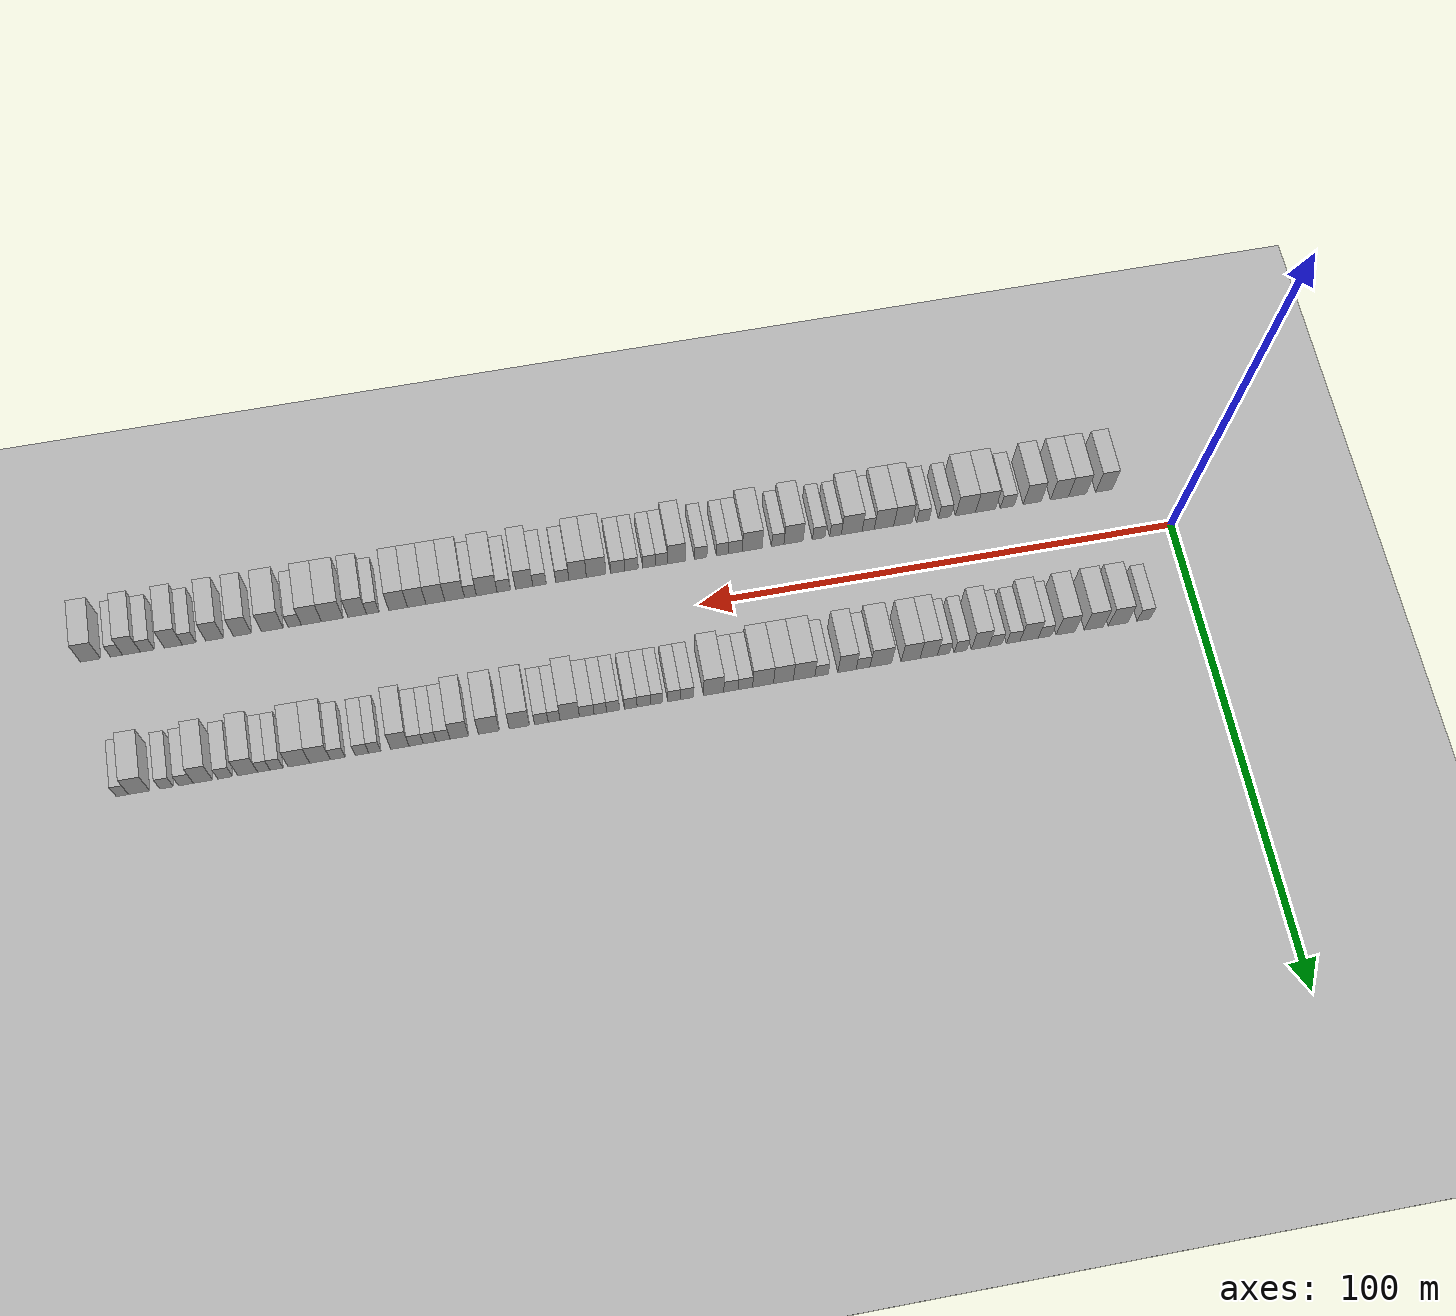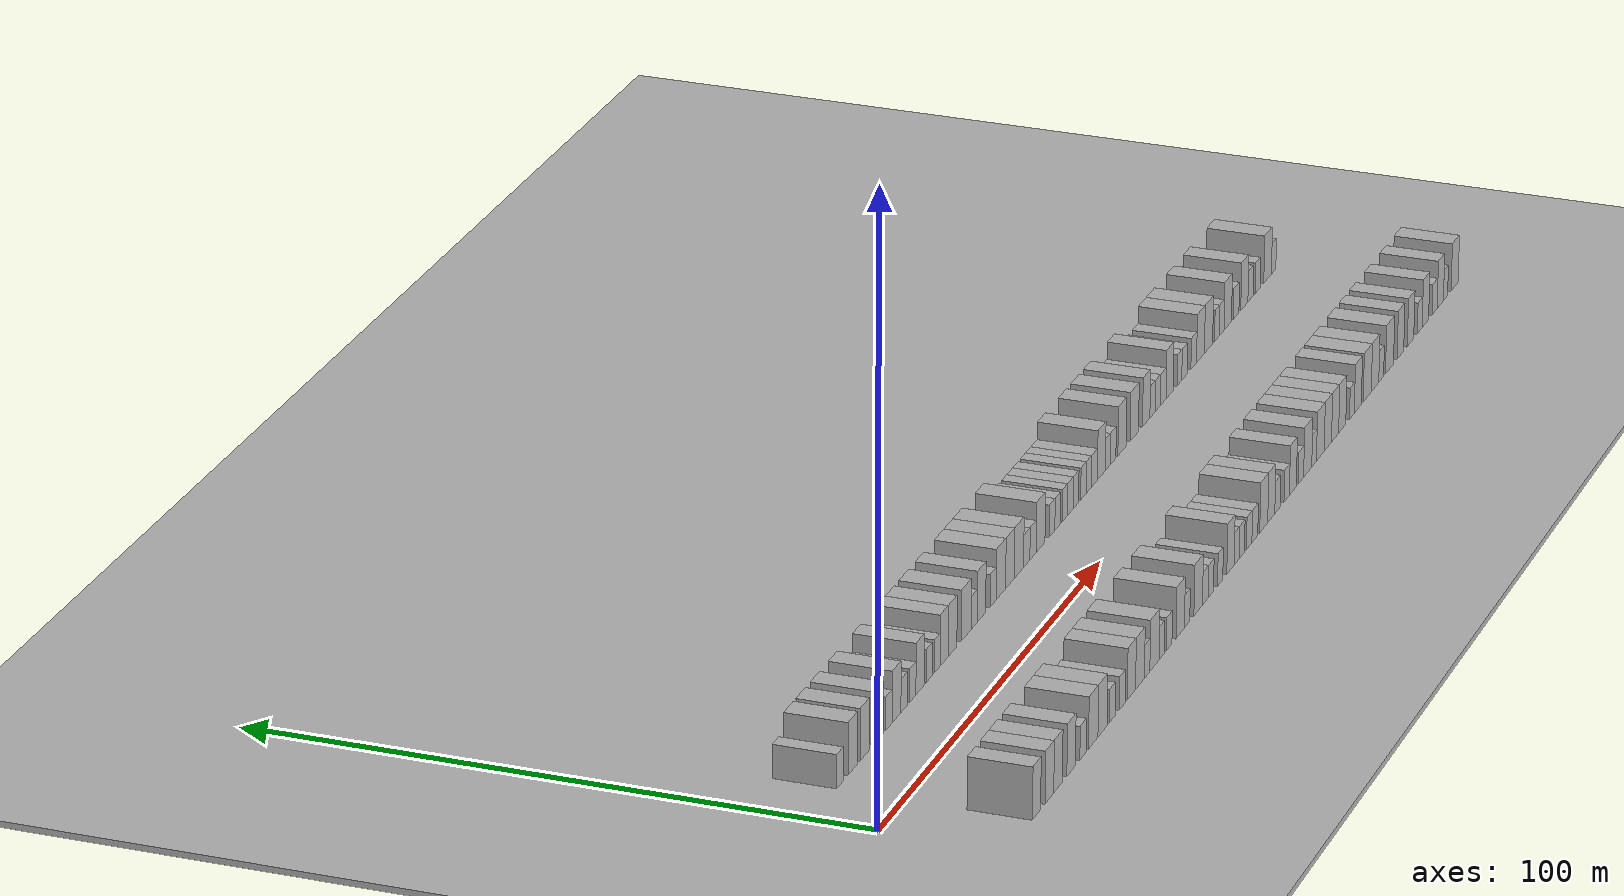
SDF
<?xml version="1.0" encoding="utf-8"?>

<sdf version="1.6">

   <world name="default">

      <gui fullscreen="0">

         <camera name="user_camera">

            <pose>-15 0 4.57585 0 0 0</pose>

            <view_controller>orbit</view_controller>

         </camera>

      </gui>

      <scene>

         <sky>

           <clouds>

             <speed>12</speed>

           </clouds>

         </sky>

         <ambient>0.4 0.4 0.4 1</ambient>

         <background>0.7 0.7 0.7 1</background>

         <shadows>1</shadows>

      </scene>

      <gravity>0 0 -9.8066</gravity>

      <magnetic_field>6e-06 2.3e-05 -4.2e-05</magnetic_field>

      <physics default="0" name="default_physics" type="ode">

         <ode>

            <solver>

               <type>quick</type>

               <iters>10</iters>

               <sor>1.0</sor>

               <use_dynamic_moi_rescaling>0</use_dynamic_moi_rescaling>

            </solver>

            <constraints>

               <cfm>0</cfm>

               <erp>0.2</erp>

               <contact_max_correcting_vel>100</contact_max_correcting_vel>

               <contact_surface_layer>0.001</contact_surface_layer>

            </constraints>

         </ode>

         <max_step_size>0.004</max_step_size>

         <real_time_factor>1</real_time_factor>

         <real_time_update_rate>250</real_time_update_rate>

      </physics>

      <light name="sun" type="directional">

         <cast_shadows>1</cast_shadows>

         <pose>0 0 10 0 0 0</pose>

         <diffuse>0.8 0.8 0.8 1</diffuse>

         <specular>0.2 0.2 0.2 1</specular>

         <attenuation>

            <range>1000</range>

            <constant>0.9</constant>

            <linear>0.01</linear>

            <quadratic>0.001</quadratic>

         </attenuation>

         <direction>-0.5 0.1 -0.9</direction>

      </light>

      <include>

         <name>ground_plane_1</name>

         <uri>model://HANNAS_ground_plane</uri>

         <pose>0 0 0  0 0 0</pose>

      </include>

      <include>

         <name>ground_plane_2</name>

         <uri>model://HANNAS_ground_plane</uri>

         <pose>100 0 0  0 0 0</pose>

      </include>

      <model name="building_1">

         <static>1</static>

         <pose frame="">11.3828 15.0000 0 0.000000 0.000000 1.570796</pose>

         <link name="link">

            <pose frame="">0 0 3.00 0 0 0</pose>

            <collision name="collision">

               <geometry>

                  <box>

                     <size>10.0000 2.7655 6.0000</size>

                  </box>

               </geometry>

               <max_contacts>10</max_contacts>

               <surface>

                  <contact>

                     <ode/>

                  </contact>

                  <bounce/>

                  <friction>

                     <torsional>

                        <ode/>

                     </torsional>

                     <ode/>

                  </friction>

               </surface>

            </collision>

            <visual name="visual">

               <cast_shadows>0</cast_shadows>

               <geometry>

                  <box>

                     <size>10.0000 2.7655 6.0000</size>

                  </box>

               </geometry>

               <material>

                  <script>

                     <uri>model://HANNAS_wall/materials/scripts</uri>

                     <uri>model://HANNAS_wall/materials/textures</uri>

                     <name>vrc/HANNAS_wall</name>

                  </script>

               </material>

            </visual>

            <self_collide>0</self_collide>

            <enable_wind>0</enable_wind>

            <kinematic>0</kinematic>

         </link>

      </model>

      <model name="building_2">

         <static>1</static>

         <pose frame="">16.8109 15.0000 0 0.000000 0.000000 1.570796</pose>

         <link name="link">

            <pose frame="">0 0 4.50 0 0 0</pose>

            <collision name="collision">

               <geometry>

                  <box>

                     <size>10.0000 4.0907 9.0000</size>

                  </box>

               </geometry>

               <max_contacts>10</max_contacts>

               <surface>

                  <contact>

                     <ode/>

                  </contact>

                  <bounce/>

                  <friction>

                     <torsional>

                        <ode/>

                     </torsional>

                     <ode/>

                  </friction>

               </surface>

            </collision>

            <visual name="visual">

               <cast_shadows>0</cast_shadows>

               <geometry>

                  <box>

                     <size>10.0000 4.0907 9.0000</size>

                  </box>

               </geometry>

               <material>

                  <script>

                     <uri>model://HANNAS_wall/materials/scripts</uri>

                     <uri>model://HANNAS_wall/materials/textures</uri>

                     <name>vrc/HANNAS_wall</name>

                  </script>

               </material>

            </visual>

            <self_collide>0</self_collide>

            <enable_wind>0</enable_wind>

            <kinematic>0</kinematic>

         </link>

      </model>

      <model name="building_3">

         <static>1</static>

         <pose frame="">21.8706 15.0000 0 0.000000 0.000000 1.570796</pose>

         <link name="link">

            <pose frame="">0 0 4.50 0 0 0</pose>

            <collision name="collision">

               <geometry>

                  <box>

                     <size>10.0000 4.0287 9.0000</size>

                  </box>

               </geometry>

               <max_contacts>10</max_contacts>

               <surface>

                  <contact>

                     <ode/>

                  </contact>

                  <bounce/>

                  <friction>

                     <torsional>

                        <ode/>

                     </torsional>

                     <ode/>

                  </friction>

               </surface>

            </collision>

            <visual name="visual">

               <cast_shadows>0</cast_shadows>

               <geometry>

                  <box>

                     <size>10.0000 4.0287 9.0000</size>

                  </box>

               </geometry>

               <material>

                  <script>

                     <uri>model://HANNAS_wall/materials/scripts</uri>

                     <uri>model://HANNAS_wall/materials/textures</uri>

                     <name>vrc/HANNAS_wall</name>

                  </script>

               </material>

            </visual>

            <self_collide>0</self_collide>

            <enable_wind>0</enable_wind>

            <kinematic>0</kinematic>

         </link>

      </model>

      <model name="building_4">

         <static>1</static>

         <pose frame="">27.8541 15.0000 0 0.000000 0.000000 1.570796</pose>

         <link name="link">

            <pose frame="">0 0 4.50 0 0 0</pose>

            <collision name="collision">

               <geometry>

                  <box>

                     <size>10.0000 3.9383 9.0000</size>

                  </box>

               </geometry>

               <max_contacts>10</max_contacts>

               <surface>

                  <contact>

                     <ode/>

                  </contact>

                  <bounce/>

                  <friction>

                     <torsional>

                        <ode/>

                     </torsional>

                     <ode/>

                  </friction>

               </surface>

            </collision>

            <visual name="visual">

               <cast_shadows>0</cast_shadows>

               <geometry>

                  <box>

                     <size>10.0000 3.9383 9.0000</size>

                  </box>

               </geometry>

               <material>

                  <script>

                     <uri>model://HANNAS_wall/materials/scripts</uri>

                     <uri>model://HANNAS_wall/materials/textures</uri>

                     <name>vrc/HANNAS_wall</name>

                  </script>

               </material>

            </visual>

            <self_collide>0</self_collide>

            <enable_wind>0</enable_wind>

            <kinematic>0</kinematic>

         </link>

      </model>

      <model name="building_5">

         <static>1</static>

         <pose frame="">32.1938 15.0000 0 0.000000 0.000000 1.570796</pose>

         <link name="link">

            <pose frame="">0 0 3.00 0 0 0</pose>

            <collision name="collision">

               <geometry>

                  <box>

                     <size>10.0000 2.7412 6.0000</size>

                  </box>

               </geometry>

               <max_contacts>10</max_contacts>

               <surface>

                  <contact>

                     <ode/>

                  </contact>

                  <bounce/>

                  <friction>

                     <torsional>

                        <ode/>

                     </torsional>

                     <ode/>

                  </friction>

               </surface>

            </collision>

            <visual name="visual">

               <cast_shadows>0</cast_shadows>

               <geometry>

                  <box>

                     <size>10.0000 2.7412 6.0000</size>

                  </box>

               </geometry>

               <material>

                  <script>

                     <uri>model://HANNAS_wall/materials/scripts</uri>

                     <uri>model://HANNAS_wall/materials/textures</uri>

                     <name>vrc/HANNAS_wall</name>

                  </script>

               </material>

            </visual>

            <self_collide>0</self_collide>

            <enable_wind>0</enable_wind>

            <kinematic>0</kinematic>

         </link>

      </model>

      <model name="building_6">

         <static>1</static>

         <pose frame="">35.4792 15.0000 0 0.000000 0.000000 1.570796</pose>

         <link name="link">

            <pose frame="">0 0 4.50 0 0 0</pose>

            <collision name="collision">

               <geometry>

                  <box>

                     <size>10.0000 3.8296 9.0000</size>

                  </box>

               </geometry>

               <max_contacts>10</max_contacts>

               <surface>

                  <contact>

                     <ode/>

                  </contact>

                  <bounce/>

                  <friction>

                     <torsional>

                        <ode/>

                     </torsional>

                     <ode/>

                  </friction>

               </surface>

            </collision>

            <visual name="visual">

               <cast_shadows>0</cast_shadows>

               <geometry>

                  <box>

                     <size>10.0000 3.8296 9.0000</size>

                  </box>

               </geometry>

               <material>

                  <script>

                     <uri>model://HANNAS_wall/materials/scripts</uri>

                     <uri>model://HANNAS_wall/materials/textures</uri>

                     <name>vrc/HANNAS_wall</name>

                  </script>

               </material>

            </visual>

            <self_collide>0</self_collide>

            <enable_wind>0</enable_wind>

            <kinematic>0</kinematic>

         </link>

      </model>

      <model name="building_7">

         <static>1</static>

         <pose frame="">38.8080 15.0000 0 0.000000 0.000000 1.570796</pose>

         <link name="link">

            <pose frame="">0 0 3.00 0 0 0</pose>

            <collision name="collision">

               <geometry>

                  <box>

                     <size>10.0000 2.8279 6.0000</size>

                  </box>

               </geometry>

               <max_contacts>10</max_contacts>

               <surface>

                  <contact>

                     <ode/>

                  </contact>

                  <bounce/>

                  <friction>

                     <torsional>

                        <ode/>

                     </torsional>

                     <ode/>

                  </friction>

               </surface>

            </collision>

            <visual name="visual">

               <cast_shadows>0</cast_shadows>

               <geometry>

                  <box>

                     <size>10.0000 2.8279 6.0000</size>

                  </box>

               </geometry>

               <material>

                  <script>

                     <uri>model://HANNAS_wall/materials/scripts</uri>

                     <uri>model://HANNAS_wall/materials/textures</uri>

                     <name>vrc/HANNAS_wall</name>

                  </script>

               </material>

            </visual>

            <self_collide>0</self_collide>

            <enable_wind>0</enable_wind>

            <kinematic>0</kinematic>

         </link>

      </model>

      <model name="building_8">

         <static>1</static>

         <pose frame="">42.5889 15.0000 0 0.000000 0.000000 1.570796</pose>

         <link name="link">

            <pose frame="">0 0 3.00 0 0 0</pose>

            <collision name="collision">

               <geometry>

                  <box>

                     <size>10.0000 2.7339 6.0000</size>

                  </box>

               </geometry>

               <max_contacts>10</max_contacts>

               <surface>

                  <contact>

                     <ode/>

                  </contact>

                  <bounce/>

                  <friction>

                     <torsional>

                        <ode/>

                     </torsional>

                     <ode/>

                  </friction>

               </surface>

            </collision>

            <visual name="visual">

               <cast_shadows>0</cast_shadows>

               <geometry>

                  <box>

                     <size>10.0000 2.7339 6.0000</size>

                  </box>

               </geometry>

               <material>

                  <script>

                     <uri>model://HANNAS_wall/materials/scripts</uri>

                     <uri>model://HANNAS_wall/materials/textures</uri>

                     <name>vrc/HANNAS_wall</name>

                  </script>

               </material>

            </visual>

            <self_collide>0</self_collide>

            <enable_wind>0</enable_wind>

            <kinematic>0</kinematic>

         </link>

      </model>

      <model name="building_9">

         <static>1</static>

         <pose frame="">45.7597 15.0000 0 0.000000 0.000000 1.570796</pose>

         <link name="link">

            <pose frame="">0 0 4.50 0 0 0</pose>

            <collision name="collision">

               <geometry>

                  <box>

                     <size>10.0000 3.6075 9.0000</size>

                  </box>

               </geometry>

               <max_contacts>10</max_contacts>

               <surface>

                  <contact>

                     <ode/>

                  </contact>

                  <bounce/>

                  <friction>

                     <torsional>

                        <ode/>

                     </torsional>

                     <ode/>

                  </friction>

               </surface>

            </collision>

            <visual name="visual">

               <cast_shadows>0</cast_shadows>

               <geometry>

                  <box>

                     <size>10.0000 3.6075 9.0000</size>

                  </box>

               </geometry>

               <material>

                  <script>

                     <uri>model://HANNAS_wall/materials/scripts</uri>

                     <uri>model://HANNAS_wall/materials/textures</uri>

                     <name>vrc/HANNAS_wall</name>

                  </script>

               </material>

            </visual>

            <self_collide>0</self_collide>

            <enable_wind>0</enable_wind>

            <kinematic>0</kinematic>

         </link>

      </model>

      <model name="building_10">

         <static>1</static>

         <pose frame="">49.8547 15.0000 0 0.000000 0.000000 1.570796</pose>

         <link name="link">

            <pose frame="">0 0 3.00 0 0 0</pose>

            <collision name="collision">

               <geometry>

                  <box>

                     <size>10.0000 2.5825 6.0000</size>

                  </box>

               </geometry>

               <max_contacts>10</max_contacts>

               <surface>

                  <contact>

                     <ode/>

                  </contact>

                  <bounce/>

                  <friction>

                     <torsional>

                        <ode/>

                     </torsional>

                     <ode/>

                  </friction>

               </surface>

            </collision>

            <visual name="visual">

               <cast_shadows>0</cast_shadows>

               <geometry>

                  <box>

                     <size>10.0000 2.5825 6.0000</size>

                  </box>

               </geometry>

               <material>

                  <script>

                     <uri>model://HANNAS_wall/materials/scripts</uri>

                     <uri>model://HANNAS_wall/materials/textures</uri>

                     <name>vrc/HANNAS_wall</name>

                  </script>

               </material>

            </visual>

            <self_collide>0</self_collide>

            <enable_wind>0</enable_wind>

            <kinematic>0</kinematic>

         </link>

      </model>

      <model name="building_11">

         <static>1</static>

         <pose frame="">53.3895 15.0000 0 0.000000 0.000000 1.570796</pose>

         <link name="link">

            <pose frame="">0 0 3.00 0 0 0</pose>

            <collision name="collision">

               <geometry>

                  <box>

                     <size>10.0000 2.4872 6.0000</size>

                  </box>

               </geometry>

               <max_contacts>10</max_contacts>

               <surface>

                  <contact>

                     <ode/>

                  </contact>

                  <bounce/>

                  <friction>

                     <torsional>

                        <ode/>

                     </torsional>

                     <ode/>

                  </friction>

               </surface>

            </collision>

            <visual name="visual">

               <cast_shadows>0</cast_shadows>

               <geometry>

                  <box>

                     <size>10.0000 2.4872 6.0000</size>

                  </box>

               </geometry>

               <material>

                  <script>

                     <uri>model://HANNAS_wall/materials/scripts</uri>

                     <uri>model://HANNAS_wall/materials/textures</uri>

                     <name>vrc/HANNAS_wall</name>

                  </script>

               </material>

            </visual>

            <self_collide>0</self_collide>

            <enable_wind>0</enable_wind>

            <kinematic>0</kinematic>

         </link>

      </model>

      <model name="building_12">

         <static>1</static>

         <pose frame="">56.4404 15.0000 0 0.000000 0.000000 1.570796</pose>

         <link name="link">

            <pose frame="">0 0 4.50 0 0 0</pose>

            <collision name="collision">

               <geometry>

                  <box>

                     <size>10.0000 3.6145 9.0000</size>

                  </box>

               </geometry>

               <max_contacts>10</max_contacts>

               <surface>

                  <contact>

                     <ode/>

                  </contact>

                  <bounce/>

                  <friction>

                     <torsional>

                        <ode/>

                     </torsional>

                     <ode/>

                  </friction>

               </surface>

            </collision>

            <visual name="visual">

               <cast_shadows>0</cast_shadows>

               <geometry>

                  <box>

                     <size>10.0000 3.6145 9.0000</size>

                  </box>

               </geometry>

               <material>

                  <script>

                     <uri>model://HANNAS_wall/materials/scripts</uri>

                     <uri>model://HANNAS_wall/materials/textures</uri>

                     <name>vrc/HANNAS_wall</name>

                  </script>

               </material>

            </visual>

            <self_collide>0</self_collide>

            <enable_wind>0</enable_wind>

            <kinematic>0</kinematic>

         </link>

      </model>

      <model name="building_13">

         <static>1</static>

         <pose frame="">60.2215 15.0000 0 0.000000 0.000000 1.570796</pose>

         <link name="link">

            <pose frame="">0 0 4.50 0 0 0</pose>

            <collision name="collision">

               <geometry>

                  <box>

                     <size>10.0000 3.9477 9.0000</size>

                  </box>

               </geometry>

               <max_contacts>10</max_contacts>

               <surface>

                  <contact>

                     <ode/>

                  </contact>

                  <bounce/>

                  <friction>

                     <torsional>

                        <ode/>

                     </torsional>

                     <ode/>

                  </friction>

               </surface>

            </collision>

            <visual name="visual">

               <cast_shadows>0</cast_shadows>

               <geometry>

                  <box>

                     <size>10.0000 3.9477 9.0000</size>

                  </box>

               </geometry>

               <material>

                  <script>

                     <uri>model://HANNAS_wall/materials/scripts</uri>

                     <uri>model://HANNAS_wall/materials/textures</uri>

                     <name>vrc/HANNAS_wall</name>

                  </script>

               </material>

            </visual>

            <self_collide>0</self_collide>

            <enable_wind>0</enable_wind>

            <kinematic>0</kinematic>

         </link>

      </model>

      <model name="building_14">

         <static>1</static>

         <pose frame="">66.4321 15.0000 0 0.000000 0.000000 1.570796</pose>

         <link name="link">

            <pose frame="">0 0 4.50 0 0 0</pose>

            <collision name="collision">

               <geometry>

                  <box>

                     <size>10.0000 4.4736 9.0000</size>

                  </box>

               </geometry>

               <max_contacts>10</max_contacts>

               <surface>

                  <contact>

                     <ode/>

                  </contact>

                  <bounce/>

                  <friction>

                     <torsional>

                        <ode/>

                     </torsional>

                     <ode/>

                  </friction>

               </surface>

            </collision>

            <visual name="visual">

               <cast_shadows>0</cast_shadows>

               <geometry>

                  <box>

                     <size>10.0000 4.4736 9.0000</size>

                  </box>

               </geometry>

               <material>

                  <script>

                     <uri>model://HANNAS_wall/materials/scripts</uri>

                     <uri>model://HANNAS_wall/materials/textures</uri>

                     <name>vrc/HANNAS_wall</name>

                  </script>

               </material>

            </visual>

            <self_collide>0</self_collide>

            <enable_wind>0</enable_wind>

            <kinematic>0</kinematic>

         </link>

      </model>

      <model name="building_15">

         <static>1</static>

         <pose frame="">70.0951 15.0000 0 0.000000 0.000000 1.570796</pose>

         <link name="link">

            <pose frame="">0 0 3.00 0 0 0</pose>

            <collision name="collision">

               <geometry>

                  <box>

                     <size>10.0000 2.8523 6.0000</size>

                  </box>

               </geometry>

               <max_contacts>10</max_contacts>

               <surface>

                  <contact>

                     <ode/>

                  </contact>

                  <bounce/>

                  <friction>

                     <torsional>

                        <ode/>

                     </torsional>

                     <ode/>

                  </friction>

               </surface>

            </collision>

            <visual name="visual">

               <cast_shadows>0</cast_shadows>

               <geometry>

                  <box>

                     <size>10.0000 2.8523 6.0000</size>

                  </box>

               </geometry>

               <material>

                  <script>

                     <uri>model://HANNAS_wall/materials/scripts</uri>

                     <uri>model://HANNAS_wall/materials/textures</uri>

                     <name>vrc/HANNAS_wall</name>

                  </script>

               </material>

            </visual>

            <self_collide>0</self_collide>

            <enable_wind>0</enable_wind>

            <kinematic>0</kinematic>

         </link>

      </model>

      <model name="building_16">

         <static>1</static>

         <pose frame="">73.4118 15.0000 0 0.000000 0.000000 1.570796</pose>

         <link name="link">

            <pose frame="">0 0 4.50 0 0 0</pose>

            <collision name="collision">

               <geometry>

                  <box>

                     <size>10.0000 3.7812 9.0000</size>

                  </box>

               </geometry>

               <max_contacts>10</max_contacts>

               <surface>

                  <contact>

                     <ode/>

                  </contact>

                  <bounce/>

                  <friction>

                     <torsional>

                        <ode/>

                     </torsional>

                     <ode/>

                  </friction>

               </surface>

            </collision>

            <visual name="visual">

               <cast_shadows>0</cast_shadows>

               <geometry>

                  <box>

                     <size>10.0000 3.7812 9.0000</size>

                  </box>

               </geometry>

               <material>

                  <script>

                     <uri>model://HANNAS_wall/materials/scripts</uri>

                     <uri>model://HANNAS_wall/materials/textures</uri>

                     <name>vrc/HANNAS_wall</name>

                  </script>

               </material>

            </visual>

            <self_collide>0</self_collide>

            <enable_wind>0</enable_wind>

            <kinematic>0</kinematic>

         </link>

      </model>

      <model name="building_17">

         <static>1</static>

         <pose frame="">78.6862 15.0000 0 0.000000 0.000000 1.570796</pose>

         <link name="link">

            <pose frame="">0 0 3.00 0 0 0</pose>

            <collision name="collision">

               <geometry>

                  <box>

                     <size>10.0000 2.7675 6.0000</size>

                  </box>

               </geometry>

               <max_contacts>10</max_contacts>

               <surface>

                  <contact>

                     <ode/>

                  </contact>

                  <bounce/>

                  <friction>

                     <torsional>

                        <ode/>

                     </torsional>

                     <ode/>

                  </friction>

               </surface>

            </collision>

            <visual name="visual">

               <cast_shadows>0</cast_shadows>

               <geometry>

                  <box>

                     <size>10.0000 2.7675 6.0000</size>

                  </box>

               </geometry>

               <material>

                  <script>

                     <uri>model://HANNAS_wall/materials/scripts</uri>

                     <uri>model://HANNAS_wall/materials/textures</uri>

                     <name>vrc/HANNAS_wall</name>

                  </script>

               </material>

            </visual>

            <self_collide>0</self_collide>

            <enable_wind>0</enable_wind>

            <kinematic>0</kinematic>

         </link>

      </model>

      <model name="building_18">

         <static>1</static>

         <pose frame="">82.2870 15.0000 0 0.000000 0.000000 1.570796</pose>

         <link name="link">

            <pose frame="">0 0 4.50 0 0 0</pose>

            <collision name="collision">

               <geometry>

                  <box>

                     <size>10.0000 4.4342 9.0000</size>

                  </box>

               </geometry>

               <max_contacts>10</max_contacts>

               <surface>

                  <contact>

                     <ode/>

                  </contact>

                  <bounce/>

                  <friction>

                     <torsional>

                        <ode/>

                     </torsional>

                     <ode/>

                  </friction>

               </surface>

            </collision>

            <visual name="visual">

               <cast_shadows>0</cast_shadows>

               <geometry>

                  <box>

                     <size>10.0000 4.4342 9.0000</size>

                  </box>

               </geometry>

               <material>

                  <script>

                     <uri>model://HANNAS_wall/materials/scripts</uri>

                     <uri>model://HANNAS_wall/materials/textures</uri>

                     <name>vrc/HANNAS_wall</name>

                  </script>

               </material>

            </visual>

            <self_collide>0</self_collide>

            <enable_wind>0</enable_wind>

            <kinematic>0</kinematic>

         </link>

      </model>

      <model name="building_19">

         <static>1</static>

         <pose frame="">86.5421 15.0000 0 0.000000 0.000000 1.570796</pose>

         <link name="link">

            <pose frame="">0 0 4.50 0 0 0</pose>

            <collision name="collision">

               <geometry>

                  <box>

                     <size>10.0000 4.0760 9.0000</size>

                  </box>

               </geometry>

               <max_contacts>10</max_contacts>

               <surface>

                  <contact>

                     <ode/>

                  </contact>

                  <bounce/>

                  <friction>

                     <torsional>

                        <ode/>

                     </torsional>

                     <ode/>

                  </friction>

               </surface>

            </collision>

            <visual name="visual">

               <cast_shadows>0</cast_shadows>

               <geometry>

                  <box>

                     <size>10.0000 4.0760 9.0000</size>

                  </box>

               </geometry>

               <material>

                  <script>

                     <uri>model://HANNAS_wall/materials/scripts</uri>

                     <uri>model://HANNAS_wall/materials/textures</uri>

                     <name>vrc/HANNAS_wall</name>

                  </script>

               </material>

            </visual>

            <self_collide>0</self_collide>

            <enable_wind>0</enable_wind>

            <kinematic>0</kinematic>

         </link>

      </model>

      <model name="building_20">

         <static>1</static>

         <pose frame="">90.7308 15.0000 0 0.000000 0.000000 1.570796</pose>

         <link name="link">

            <pose frame="">0 0 4.50 0 0 0</pose>

            <collision name="collision">

               <geometry>

                  <box>

                     <size>10.0000 4.3013 9.0000</size>

                  </box>

               </geometry>

               <max_contacts>10</max_contacts>

               <surface>

                  <contact>

                     <ode/>

                  </contact>

                  <bounce/>

                  <friction>

                     <torsional>

                        <ode/>

                     </torsional>

                     <ode/>

                  </friction>

               </surface>

            </collision>

            <visual name="visual">

               <cast_shadows>0</cast_shadows>

               <geometry>

                  <box>

                     <size>10.0000 4.3013 9.0000</size>

                  </box>

               </geometry>

               <material>

                  <script>

                     <uri>model://HANNAS_wall/materials/scripts</uri>

                     <uri>model://HANNAS_wall/materials/textures</uri>

                     <name>vrc/HANNAS_wall</name>

                  </script>

               </material>

            </visual>

            <self_collide>0</self_collide>

            <enable_wind>0</enable_wind>

            <kinematic>0</kinematic>

         </link>

      </model>

      <model name="building_21">

         <static>1</static>

         <pose frame="">94.3463 15.0000 0 0.000000 0.000000 1.570796</pose>

         <link name="link">

            <pose frame="">0 0 3.00 0 0 0</pose>

            <collision name="collision">

               <geometry>

                  <box>

                     <size>10.0000 2.9298 6.0000</size>

                  </box>

               </geometry>

               <max_contacts>10</max_contacts>

               <surface>

                  <contact>

                     <ode/>

                  </contact>

                  <bounce/>

                  <friction>

                     <torsional>

                        <ode/>

                     </torsional>

                     <ode/>

                  </friction>

               </surface>

            </collision>

            <visual name="visual">

               <cast_shadows>0</cast_shadows>

               <geometry>

                  <box>

                     <size>10.0000 2.9298 6.0000</size>

                  </box>

               </geometry>

               <material>

                  <script>

                     <uri>model://HANNAS_wall/materials/scripts</uri>

                     <uri>model://HANNAS_wall/materials/textures</uri>

                     <name>vrc/HANNAS_wall</name>

                  </script>

               </material>

            </visual>

            <self_collide>0</self_collide>

            <enable_wind>0</enable_wind>

            <kinematic>0</kinematic>

         </link>

      </model>

      <model name="building_22">

         <static>1</static>

         <pose frame="">97.3043 15.0000 0 0.000000 0.000000 1.570796</pose>

         <link name="link">

            <pose frame="">0 0 3.00 0 0 0</pose>

            <collision name="collision">

               <geometry>

                  <box>

                     <size>10.0000 2.9861 6.0000</size>

                  </box>

               </geometry>

               <max_contacts>10</max_contacts>

               <surface>

                  <contact>

                     <ode/>

                  </contact>

                  <bounce/>

                  <friction>

                     <torsional>

                        <ode/>

                     </torsional>

                     <ode/>

                  </friction>

               </surface>

            </collision>

            <visual name="visual">

               <cast_shadows>0</cast_shadows>

               <geometry>

                  <box>

                     <size>10.0000 2.9861 6.0000</size>

                  </box>

               </geometry>

               <material>

                  <script>

                     <uri>model://HANNAS_wall/materials/scripts</uri>

                     <uri>model://HANNAS_wall/materials/textures</uri>

                     <name>vrc/HANNAS_wall</name>

                  </script>

               </material>

            </visual>

            <self_collide>0</self_collide>

            <enable_wind>0</enable_wind>

            <kinematic>0</kinematic>

         </link>

      </model>

      <model name="building_23">

         <static>1</static>

         <pose frame="">100.8639 15.0000 0 0.000000 0.000000 1.570796</pose>

         <link name="link">

            <pose frame="">0 0 4.50 0 0 0</pose>

            <collision name="collision">

               <geometry>

                  <box>

                     <size>10.0000 4.1332 9.0000</size>

                  </box>

               </geometry>

               <max_contacts>10</max_contacts>

               <surface>

                  <contact>

                     <ode/>

                  </contact>

                  <bounce/>

                  <friction>

                     <torsional>

                        <ode/>

                     </torsional>

                     <ode/>

                  </friction>

               </surface>

            </collision>

            <visual name="visual">

               <cast_shadows>0</cast_shadows>

               <geometry>

                  <box>

                     <size>10.0000 4.1332 9.0000</size>

                  </box>

               </geometry>

               <material>

                  <script>

                     <uri>model://HANNAS_wall/materials/scripts</uri>

                     <uri>model://HANNAS_wall/materials/textures</uri>

                     <name>vrc/HANNAS_wall</name>

                  </script>

               </material>

            </visual>

            <self_collide>0</self_collide>

            <enable_wind>0</enable_wind>

            <kinematic>0</kinematic>

         </link>

      </model>

      <model name="building_24">

         <static>1</static>

         <pose frame="">106.2925 15.0000 0 0.000000 0.000000 1.570796</pose>

         <link name="link">

            <pose frame="">0 0 3.00 0 0 0</pose>

            <collision name="collision">

               <geometry>

                  <box>

                     <size>10.0000 2.7241 6.0000</size>

                  </box>

               </geometry>

               <max_contacts>10</max_contacts>

               <surface>

                  <contact>

                     <ode/>

                  </contact>

                  <bounce/>

                  <friction>

                     <torsional>

                        <ode/>

                     </torsional>

                     <ode/>

                  </friction>

               </surface>

            </collision>

            <visual name="visual">

               <cast_shadows>0</cast_shadows>

               <geometry>

                  <box>

                     <size>10.0000 2.7241 6.0000</size>

                  </box>

               </geometry>

               <material>

                  <script>

                     <uri>model://HANNAS_wall/materials/scripts</uri>

                     <uri>model://HANNAS_wall/materials/textures</uri>

                     <name>vrc/HANNAS_wall</name>

                  </script>

               </material>

            </visual>

            <self_collide>0</self_collide>

            <enable_wind>0</enable_wind>

            <kinematic>0</kinematic>

         </link>

      </model>

      <model name="building_25">

         <static>1</static>

         <pose frame="">108.9550 15.0000 0 0.000000 0.000000 1.570796</pose>

         <link name="link">

            <pose frame="">0 0 3.00 0 0 0</pose>

            <collision name="collision">

               <geometry>

                  <box>

                     <size>10.0000 2.6010 6.0000</size>

                  </box>

               </geometry>

               <max_contacts>10</max_contacts>

               <surface>

                  <contact>

                     <ode/>

                  </contact>

                  <bounce/>

                  <friction>

                     <torsional>

                        <ode/>

                     </torsional>

                     <ode/>

                  </friction>

               </surface>

            </collision>

            <visual name="visual">

               <cast_shadows>0</cast_shadows>

               <geometry>

                  <box>

                     <size>10.0000 2.6010 6.0000</size>

                  </box>

               </geometry>

               <material>

                  <script>

                     <uri>model://HANNAS_wall/materials/scripts</uri>

                     <uri>model://HANNAS_wall/materials/textures</uri>

                     <name>vrc/HANNAS_wall</name>

                  </script>

               </material>

            </visual>

            <self_collide>0</self_collide>

            <enable_wind>0</enable_wind>

            <kinematic>0</kinematic>

         </link>

      </model>

      <model name="building_26">

         <static>1</static>

         <pose frame="">112.4720 15.0000 0 0.000000 0.000000 1.570796</pose>

         <link name="link">

            <pose frame="">0 0 3.00 0 0 0</pose>

            <collision name="collision">

               <geometry>

                  <box>

                     <size>10.0000 2.4330 6.0000</size>

                  </box>

               </geometry>

               <max_contacts>10</max_contacts>

               <surface>

                  <contact>

                     <ode/>

                  </contact>

                  <bounce/>

                  <friction>

                     <torsional>

                        <ode/>

                     </torsional>

                     <ode/>

                  </friction>

               </surface>

            </collision>

            <visual name="visual">

               <cast_shadows>0</cast_shadows>

               <geometry>

                  <box>

                     <size>10.0000 2.4330 6.0000</size>

                  </box>

               </geometry>

               <material>

                  <script>

                     <uri>model://HANNAS_wall/materials/scripts</uri>

                     <uri>model://HANNAS_wall/materials/textures</uri>

                     <name>vrc/HANNAS_wall</name>

                  </script>

               </material>

            </visual>

            <self_collide>0</self_collide>

            <enable_wind>0</enable_wind>

            <kinematic>0</kinematic>

         </link>

      </model>

      <model name="building_27">

         <static>1</static>

         <pose frame="">115.1053 15.0000 0 0.000000 0.000000 1.570796</pose>

         <link name="link">

            <pose frame="">0 0 3.00 0 0 0</pose>

            <collision name="collision">

               <geometry>

                  <box>

                     <size>10.0000 2.8334 6.0000</size>

                  </box>

               </geometry>

               <max_contacts>10</max_contacts>

               <surface>

                  <contact>

                     <ode/>

                  </contact>

                  <bounce/>

                  <friction>

                     <torsional>

                        <ode/>

                     </torsional>

                     <ode/>

                  </friction>

               </surface>

            </collision>

            <visual name="visual">

               <cast_shadows>0</cast_shadows>

               <geometry>

                  <box>

                     <size>10.0000 2.8334 6.0000</size>

                  </box>

               </geometry>

               <material>

                  <script>

                     <uri>model://HANNAS_wall/materials/scripts</uri>

                     <uri>model://HANNAS_wall/materials/textures</uri>

                     <name>vrc/HANNAS_wall</name>

                  </script>

               </material>

            </visual>

            <self_collide>0</self_collide>

            <enable_wind>0</enable_wind>

            <kinematic>0</kinematic>

         </link>

      </model>

      <model name="building_28">

         <static>1</static>

         <pose frame="">117.8139 15.0000 0 0.000000 0.000000 1.570796</pose>

         <link name="link">

            <pose frame="">0 0 3.00 0 0 0</pose>

            <collision name="collision">

               <geometry>

                  <box>

                     <size>10.0000 2.5838 6.0000</size>

                  </box>

               </geometry>

               <max_contacts>10</max_contacts>

               <surface>

                  <contact>

                     <ode/>

                  </contact>

                  <bounce/>

                  <friction>

                     <torsional>

                        <ode/>

                     </torsional>

                     <ode/>

                  </friction>

               </surface>

            </collision>

            <visual name="visual">

               <cast_shadows>0</cast_shadows>

               <geometry>

                  <box>

                     <size>10.0000 2.5838 6.0000</size>

                  </box>

               </geometry>

               <material>

                  <script>

                     <uri>model://HANNAS_wall/materials/scripts</uri>

                     <uri>model://HANNAS_wall/materials/textures</uri>

                     <name>vrc/HANNAS_wall</name>

                  </script>

               </material>

            </visual>

            <self_collide>0</self_collide>

            <enable_wind>0</enable_wind>

            <kinematic>0</kinematic>

         </link>

      </model>

      <model name="building_29">

         <static>1</static>

         <pose frame="">121.4289 15.0000 0 0.000000 0.000000 1.570796</pose>

         <link name="link">

            <pose frame="">0 0 3.00 0 0 0</pose>

            <collision name="collision">

               <geometry>

                  <box>

                     <size>10.0000 2.6463 6.0000</size>

                  </box>

               </geometry>

               <max_contacts>10</max_contacts>

               <surface>

                  <contact>

                     <ode/>

                  </contact>

                  <bounce/>

                  <friction>

                     <torsional>

                        <ode/>

                     </torsional>

                     <ode/>

                  </friction>

               </surface>

            </collision>

            <visual name="visual">

               <cast_shadows>0</cast_shadows>

               <geometry>

                  <box>

                     <size>10.0000 2.6463 6.0000</size>

                  </box>

               </geometry>

               <material>

                  <script>

                     <uri>model://HANNAS_wall/materials/scripts</uri>

                     <uri>model://HANNAS_wall/materials/textures</uri>

                     <name>vrc/HANNAS_wall</name>

                  </script>

               </material>

            </visual>

            <self_collide>0</self_collide>

            <enable_wind>0</enable_wind>

            <kinematic>0</kinematic>

         </link>

      </model>

      <model name="building_30">

         <static>1</static>

         <pose frame="">124.0147 15.0000 0 0.000000 0.000000 1.570796</pose>

         <link name="link">

            <pose frame="">0 0 3.00 0 0 0</pose>

            <collision name="collision">

               <geometry>

                  <box>

                     <size>10.0000 2.5252 6.0000</size>

                  </box>

               </geometry>

               <max_contacts>10</max_contacts>

               <surface>

                  <contact>

                     <ode/>

                  </contact>

                  <bounce/>

                  <friction>

                     <torsional>

                        <ode/>

                     </torsional>

                     <ode/>

                  </friction>

               </surface>

            </collision>

            <visual name="visual">

               <cast_shadows>0</cast_shadows>

               <geometry>

                  <box>

                     <size>10.0000 2.5252 6.0000</size>

                  </box>

               </geometry>

               <material>

                  <script>

                     <uri>model://HANNAS_wall/materials/scripts</uri>

                     <uri>model://HANNAS_wall/materials/textures</uri>

                     <name>vrc/HANNAS_wall</name>

                  </script>

               </material>

            </visual>

            <self_collide>0</self_collide>

            <enable_wind>0</enable_wind>

            <kinematic>0</kinematic>

         </link>

      </model>

      <model name="building_31">

         <static>1</static>

         <pose frame="">126.7726 15.0000 0 0.000000 0.000000 1.570796</pose>

         <link name="link">

            <pose frame="">0 0 3.00 0 0 0</pose>

            <collision name="collision">

               <geometry>

                  <box>

                     <size>10.0000 2.9906 6.0000</size>

                  </box>

               </geometry>

               <max_contacts>10</max_contacts>

               <surface>

                  <contact>

                     <ode/>

                  </contact>

                  <bounce/>

                  <friction>

                     <torsional>

                        <ode/>

                     </torsional>

                     <ode/>

                  </friction>

               </surface>

            </collision>

            <visual name="visual">

               <cast_shadows>0</cast_shadows>

               <geometry>

                  <box>

                     <size>10.0000 2.9906 6.0000</size>

                  </box>

               </geometry>

               <material>

                  <script>

                     <uri>model://HANNAS_wall/materials/scripts</uri>

                     <uri>model://HANNAS_wall/materials/textures</uri>

                     <name>vrc/HANNAS_wall</name>

                  </script>

               </material>

            </visual>

            <self_collide>0</self_collide>

            <enable_wind>0</enable_wind>

            <kinematic>0</kinematic>

         </link>

      </model>

      <model name="building_32">

         <static>1</static>

         <pose frame="">130.2242 15.0000 0 0.000000 0.000000 1.570796</pose>

         <link name="link">

            <pose frame="">0 0 4.50 0 0 0</pose>

            <collision name="collision">

               <geometry>

                  <box>

                     <size>10.0000 3.9126 9.0000</size>

                  </box>

               </geometry>

               <max_contacts>10</max_contacts>

               <surface>

                  <contact>

                     <ode/>

                  </contact>

                  <bounce/>

                  <friction>

                     <torsional>

                        <ode/>

                     </torsional>

                     <ode/>

                  </friction>

               </surface>

            </collision>

            <visual name="visual">

               <cast_shadows>0</cast_shadows>

               <geometry>

                  <box>

                     <size>10.0000 3.9126 9.0000</size>

                  </box>

               </geometry>

               <material>

                  <script>

                     <uri>model://HANNAS_wall/materials/scripts</uri>

                     <uri>model://HANNAS_wall/materials/textures</uri>

                     <name>vrc/HANNAS_wall</name>

                  </script>

               </material>

            </visual>

            <self_collide>0</self_collide>

            <enable_wind>0</enable_wind>

            <kinematic>0</kinematic>

         </link>

      </model>

      <model name="building_33">

         <static>1</static>

         <pose frame="">133.3815 15.0000 0 0.000000 0.000000 1.570796</pose>

         <link name="link">

            <pose frame="">0 0 3.00 0 0 0</pose>

            <collision name="collision">

               <geometry>

                  <box>

                     <size>10.0000 2.4020 6.0000</size>

                  </box>

               </geometry>

               <max_contacts>10</max_contacts>

               <surface>

                  <contact>

                     <ode/>

                  </contact>

                  <bounce/>

                  <friction>

                     <torsional>

                        <ode/>

                     </torsional>

                     <ode/>

                  </friction>

               </surface>

            </collision>

            <visual name="visual">

               <cast_shadows>0</cast_shadows>

               <geometry>

                  <box>

                     <size>10.0000 2.4020 6.0000</size>

                  </box>

               </geometry>

               <material>

                  <script>

                     <uri>model://HANNAS_wall/materials/scripts</uri>

                     <uri>model://HANNAS_wall/materials/textures</uri>

                     <name>vrc/HANNAS_wall</name>

                  </script>

               </material>

            </visual>

            <self_collide>0</self_collide>

            <enable_wind>0</enable_wind>

            <kinematic>0</kinematic>

         </link>

      </model>

      <model name="building_34">

         <static>1</static>

         <pose frame="">135.9725 15.0000 0 0.000000 0.000000 1.570796</pose>

         <link name="link">

            <pose frame="">0 0 3.00 0 0 0</pose>

            <collision name="collision">

               <geometry>

                  <box>

                     <size>10.0000 2.7799 6.0000</size>

                  </box>

               </geometry>

               <max_contacts>10</max_contacts>

               <surface>

                  <contact>

                     <ode/>

                  </contact>

                  <bounce/>

                  <friction>

                     <torsional>

                        <ode/>

                     </torsional>

                     <ode/>

                  </friction>

               </surface>

            </collision>

            <visual name="visual">

               <cast_shadows>0</cast_shadows>

               <geometry>

                  <box>

                     <size>10.0000 2.7799 6.0000</size>

                  </box>

               </geometry>

               <material>

                  <script>

                     <uri>model://HANNAS_wall/materials/scripts</uri>

                     <uri>model://HANNAS_wall/materials/textures</uri>

                     <name>vrc/HANNAS_wall</name>

                  </script>

               </material>

            </visual>

            <self_collide>0</self_collide>

            <enable_wind>0</enable_wind>

            <kinematic>0</kinematic>

         </link>

      </model>

      <model name="building_35">

         <static>1</static>

         <pose frame="">140.4146 15.0000 0 0.000000 0.000000 1.570796</pose>

         <link name="link">

            <pose frame="">0 0 4.50 0 0 0</pose>

            <collision name="collision">

               <geometry>

                  <box>

                     <size>10.0000 4.1042 9.0000</size>

                  </box>

               </geometry>

               <max_contacts>10</max_contacts>

               <surface>

                  <contact>

                     <ode/>

                  </contact>

                  <bounce/>

                  <friction>

                     <torsional>

                        <ode/>

                     </torsional>

                     <ode/>

                  </friction>

               </surface>

            </collision>

            <visual name="visual">

               <cast_shadows>0</cast_shadows>

               <geometry>

                  <box>

                     <size>10.0000 4.1042 9.0000</size>

                  </box>

               </geometry>

               <material>

                  <script>

                     <uri>model://HANNAS_wall/materials/scripts</uri>

                     <uri>model://HANNAS_wall/materials/textures</uri>

                     <name>vrc/HANNAS_wall</name>

                  </script>

               </material>

            </visual>

            <self_collide>0</self_collide>

            <enable_wind>0</enable_wind>

            <kinematic>0</kinematic>

         </link>

      </model>

      <model name="building_36">

         <static>1</static>

         <pose frame="">146.5782 15.0000 0 0.000000 0.000000 1.570796</pose>

         <link name="link">

            <pose frame="">0 0 4.50 0 0 0</pose>

            <collision name="collision">

               <geometry>

                  <box>

                     <size>10.0000 4.2231 9.0000</size>

                  </box>

               </geometry>

               <max_contacts>10</max_contacts>

               <surface>

                  <contact>

                     <ode/>

                  </contact>

                  <bounce/>

                  <friction>

                     <torsional>

                        <ode/>

                     </torsional>

                     <ode/>

                  </friction>

               </surface>

            </collision>

            <visual name="visual">

               <cast_shadows>0</cast_shadows>

               <geometry>

                  <box>

                     <size>10.0000 4.2231 9.0000</size>

                  </box>

               </geometry>

               <material>

                  <script>

                     <uri>model://HANNAS_wall/materials/scripts</uri>

                     <uri>model://HANNAS_wall/materials/textures</uri>

                     <name>vrc/HANNAS_wall</name>

                  </script>

               </material>

            </visual>

            <self_collide>0</self_collide>

            <enable_wind>0</enable_wind>

            <kinematic>0</kinematic>

         </link>

      </model>

      <model name="building_37">

         <static>1</static>

         <pose frame="">152.5548 15.0000 0 0.000000 0.000000 1.570796</pose>

         <link name="link">

            <pose frame="">0 0 4.50 0 0 0</pose>

            <collision name="collision">

               <geometry>

                  <box>

                     <size>10.0000 3.7300 9.0000</size>

                  </box>

               </geometry>

               <max_contacts>10</max_contacts>

               <surface>

                  <contact>

                     <ode/>

                  </contact>

                  <bounce/>

                  <friction>

                     <torsional>

                        <ode/>

                     </torsional>

                     <ode/>

                  </friction>

               </surface>

            </collision>

            <visual name="visual">

               <cast_shadows>0</cast_shadows>

               <geometry>

                  <box>

                     <size>10.0000 3.7300 9.0000</size>

                  </box>

               </geometry>

               <material>

                  <script>

                     <uri>model://HANNAS_wall/materials/scripts</uri>

                     <uri>model://HANNAS_wall/materials/textures</uri>

                     <name>vrc/HANNAS_wall</name>

                  </script>

               </material>

            </visual>

            <self_collide>0</self_collide>

            <enable_wind>0</enable_wind>

            <kinematic>0</kinematic>

         </link>

      </model>

      <model name="building_38">

         <static>1</static>

         <pose frame="">155.8073 15.0000 0 0.000000 0.000000 1.570796</pose>

         <link name="link">

            <pose frame="">0 0 3.00 0 0 0</pose>

            <collision name="collision">

               <geometry>

                  <box>

                     <size>10.0000 2.7752 6.0000</size>

                  </box>

               </geometry>

               <max_contacts>10</max_contacts>

               <surface>

                  <contact>

                     <ode/>

                  </contact>

                  <bounce/>

                  <friction>

                     <torsional>

                        <ode/>

                     </torsional>

                     <ode/>

                  </friction>

               </surface>

            </collision>

            <visual name="visual">

               <cast_shadows>0</cast_shadows>

               <geometry>

                  <box>

                     <size>10.0000 2.7752 6.0000</size>

                  </box>

               </geometry>

               <material>

                  <script>

                     <uri>model://HANNAS_wall/materials/scripts</uri>

                     <uri>model://HANNAS_wall/materials/textures</uri>

                     <name>vrc/HANNAS_wall</name>

                  </script>

               </material>

            </visual>

            <self_collide>0</self_collide>

            <enable_wind>0</enable_wind>

            <kinematic>0</kinematic>

         </link>

      </model>

      <model name="building_39">

         <static>1</static>

         <pose frame="">158.5008 15.0000 0 0.000000 0.000000 1.570796</pose>

         <link name="link">

            <pose frame="">0 0 3.00 0 0 0</pose>

            <collision name="collision">

               <geometry>

                  <box>

                     <size>10.0000 2.6118 6.0000</size>

                  </box>

               </geometry>

               <max_contacts>10</max_contacts>

               <surface>

                  <contact>

                     <ode/>

                  </contact>

                  <bounce/>

                  <friction>

                     <torsional>

                        <ode/>

                     </torsional>

                     <ode/>

                  </friction>

               </surface>

            </collision>

            <visual name="visual">

               <cast_shadows>0</cast_shadows>

               <geometry>

                  <box>

                     <size>10.0000 2.6118 6.0000</size>

                  </box>

               </geometry>

               <material>

                  <script>

                     <uri>model://HANNAS_wall/materials/scripts</uri>

                     <uri>model://HANNAS_wall/materials/textures</uri>

                     <name>vrc/HANNAS_wall</name>

                  </script>

               </material>

            </visual>

            <self_collide>0</self_collide>

            <enable_wind>0</enable_wind>

            <kinematic>0</kinematic>

         </link>

      </model>

      <model name="building_40">

         <static>1</static>

         <pose frame="">161.2350 15.0000 0 0.000000 0.000000 1.570796</pose>

         <link name="link">

            <pose frame="">0 0 3.00 0 0 0</pose>

            <collision name="collision">

               <geometry>

                  <box>

                     <size>10.0000 2.8566 6.0000</size>

                  </box>

               </geometry>

               <max_contacts>10</max_contacts>

               <surface>

                  <contact>

                     <ode/>

                  </contact>

                  <bounce/>

                  <friction>

                     <torsional>

                        <ode/>

                     </torsional>

                     <ode/>

                  </friction>

               </surface>

            </collision>

            <visual name="visual">

               <cast_shadows>0</cast_shadows>

               <geometry>

                  <box>

                     <size>10.0000 2.8566 6.0000</size>

                  </box>

               </geometry>

               <material>

                  <script>

                     <uri>model://HANNAS_wall/materials/scripts</uri>

                     <uri>model://HANNAS_wall/materials/textures</uri>

                     <name>vrc/HANNAS_wall</name>

                  </script>

               </material>

            </visual>

            <self_collide>0</self_collide>

            <enable_wind>0</enable_wind>

            <kinematic>0</kinematic>

         </link>

      </model>

      <model name="building_41">

         <static>1</static>

         <pose frame="">164.4951 15.0000 0 0.000000 0.000000 1.570796</pose>

         <link name="link">

            <pose frame="">0 0 4.50 0 0 0</pose>

            <collision name="collision">

               <geometry>

                  <box>

                     <size>10.0000 3.6636 9.0000</size>

                  </box>

               </geometry>

               <max_contacts>10</max_contacts>

               <surface>

                  <contact>

                     <ode/>

                  </contact>

                  <bounce/>

                  <friction>

                     <torsional>

                        <ode/>

                     </torsional>

                     <ode/>

                  </friction>

               </surface>

            </collision>

            <visual name="visual">

               <cast_shadows>0</cast_shadows>

               <geometry>

                  <box>

                     <size>10.0000 3.6636 9.0000</size>

                  </box>

               </geometry>

               <material>

                  <script>

                     <uri>model://HANNAS_wall/materials/scripts</uri>

                     <uri>model://HANNAS_wall/materials/textures</uri>

                     <name>vrc/HANNAS_wall</name>

                  </script>

               </material>

            </visual>

            <self_collide>0</self_collide>

            <enable_wind>0</enable_wind>

            <kinematic>0</kinematic>

         </link>

      </model>

      <model name="building_42">

         <static>1</static>

         <pose frame="">169.5368 15.0000 0 0.000000 0.000000 1.570796</pose>

         <link name="link">

            <pose frame="">0 0 3.00 0 0 0</pose>

            <collision name="collision">

               <geometry>

                  <box>

                     <size>10.0000 2.4198 6.0000</size>

                  </box>

               </geometry>

               <max_contacts>10</max_contacts>

               <surface>

                  <contact>

                     <ode/>

                  </contact>

                  <bounce/>

                  <friction>

                     <torsional>

                        <ode/>

                     </torsional>

                     <ode/>

                  </friction>

               </surface>

            </collision>

            <visual name="visual">

               <cast_shadows>0</cast_shadows>

               <geometry>

                  <box>

                     <size>10.0000 2.4198 6.0000</size>

                  </box>

               </geometry>

               <material>

                  <script>

                     <uri>model://HANNAS_wall/materials/scripts</uri>

                     <uri>model://HANNAS_wall/materials/textures</uri>

                     <name>vrc/HANNAS_wall</name>

                  </script>

               </material>

            </visual>

            <self_collide>0</self_collide>

            <enable_wind>0</enable_wind>

            <kinematic>0</kinematic>

         </link>

      </model>

      <model name="building_43">

         <static>1</static>

         <pose frame="">172.1120 15.0000 0 0.000000 0.000000 1.570796</pose>

         <link name="link">

            <pose frame="">0 0 3.00 0 0 0</pose>

            <collision name="collision">

               <geometry>

                  <box>

                     <size>10.0000 2.7305 6.0000</size>

                  </box>

               </geometry>

               <max_contacts>10</max_contacts>

               <surface>

                  <contact>

                     <ode/>

                  </contact>

                  <bounce/>

                  <friction>

                     <torsional>

                        <ode/>

                     </torsional>

                     <ode/>

                  </friction>

               </surface>

            </collision>

            <visual name="visual">

               <cast_shadows>0</cast_shadows>

               <geometry>

                  <box>

                     <size>10.0000 2.7305 6.0000</size>

                  </box>

               </geometry>

               <material>

                  <script>

                     <uri>model://HANNAS_wall/materials/scripts</uri>

                     <uri>model://HANNAS_wall/materials/textures</uri>

                     <name>vrc/HANNAS_wall</name>

                  </script>

               </material>

            </visual>

            <self_collide>0</self_collide>

            <enable_wind>0</enable_wind>

            <kinematic>0</kinematic>

         </link>

      </model>

      <model name="building_44">

         <static>1</static>

         <pose frame="">176.9571 15.0000 0 0.000000 0.000000 1.570796</pose>

         <link name="link">

            <pose frame="">0 0 3.00 0 0 0</pose>

            <collision name="collision">

               <geometry>

                  <box>

                     <size>10.0000 2.9599 6.0000</size>

                  </box>

               </geometry>

               <max_contacts>10</max_contacts>

               <surface>

                  <contact>

                     <ode/>

                  </contact>

                  <bounce/>

                  <friction>

                     <torsional>

                        <ode/>

                     </torsional>

                     <ode/>

                  </friction>

               </surface>

            </collision>

            <visual name="visual">

               <cast_shadows>0</cast_shadows>

               <geometry>

                  <box>

                     <size>10.0000 2.9599 6.0000</size>

                  </box>

               </geometry>

               <material>

                  <script>

                     <uri>model://HANNAS_wall/materials/scripts</uri>

                     <uri>model://HANNAS_wall/materials/textures</uri>

                     <name>vrc/HANNAS_wall</name>

                  </script>

               </material>

            </visual>

            <self_collide>0</self_collide>

            <enable_wind>0</enable_wind>

            <kinematic>0</kinematic>

         </link>

      </model>

      <model name="building_45">

         <static>1</static>

         <pose frame="">180.4960 15.0000 0 0.000000 0.000000 1.570796</pose>

         <link name="link">

            <pose frame="">0 0 4.50 0 0 0</pose>

            <collision name="collision">

               <geometry>

                  <box>

                     <size>10.0000 4.1179 9.0000</size>

                  </box>

               </geometry>

               <max_contacts>10</max_contacts>

               <surface>

                  <contact>

                     <ode/>

                  </contact>

                  <bounce/>

                  <friction>

                     <torsional>

                        <ode/>

                     </torsional>

                     <ode/>

                  </friction>

               </surface>

            </collision>

            <visual name="visual">

               <cast_shadows>0</cast_shadows>

               <geometry>

                  <box>

                     <size>10.0000 4.1179 9.0000</size>

                  </box>

               </geometry>

               <material>

                  <script>

                     <uri>model://HANNAS_wall/materials/scripts</uri>

                     <uri>model://HANNAS_wall/materials/textures</uri>

                     <name>vrc/HANNAS_wall</name>

                  </script>

               </material>

            </visual>

            <self_collide>0</self_collide>

            <enable_wind>0</enable_wind>

            <kinematic>0</kinematic>

         </link>

      </model>

      <model name="building_46">

         <static>1</static>

         <pose frame="">184.7159 15.0000 0 0.000000 0.000000 1.570796</pose>

         <link name="link">

            <pose frame="">0 0 4.50 0 0 0</pose>

            <collision name="collision">

               <geometry>

                  <box>

                     <size>10.0000 4.3219 9.0000</size>

                  </box>

               </geometry>

               <max_contacts>10</max_contacts>

               <surface>

                  <contact>

                     <ode/>

                  </contact>

                  <bounce/>

                  <friction>

                     <torsional>

                        <ode/>

                     </torsional>

                     <ode/>

                  </friction>

               </surface>

            </collision>

            <visual name="visual">

               <cast_shadows>0</cast_shadows>

               <geometry>

                  <box>

                     <size>10.0000 4.3219 9.0000</size>

                  </box>

               </geometry>

               <material>

                  <script>

                     <uri>model://HANNAS_wall/materials/scripts</uri>

                     <uri>model://HANNAS_wall/materials/textures</uri>

                     <name>vrc/HANNAS_wall</name>

                  </script>

               </material>

            </visual>

            <self_collide>0</self_collide>

            <enable_wind>0</enable_wind>

            <kinematic>0</kinematic>

         </link>

      </model>

      <model name="building_47">

         <static>1</static>

         <pose frame="">189.1705 15.0000 0 0.000000 0.000000 1.570796</pose>

         <link name="link">

            <pose frame="">0 0 3.00 0 0 0</pose>

            <collision name="collision">

               <geometry>

                  <box>

                     <size>10.0000 2.5874 6.0000</size>

                  </box>

               </geometry>

               <max_contacts>10</max_contacts>

               <surface>

                  <contact>

                     <ode/>

                  </contact>

                  <bounce/>

                  <friction>

                     <torsional>

                        <ode/>

                     </torsional>

                     <ode/>

                  </friction>

               </surface>

            </collision>

            <visual name="visual">

               <cast_shadows>0</cast_shadows>

               <geometry>

                  <box>

                     <size>10.0000 2.5874 6.0000</size>

                  </box>

               </geometry>

               <material>

                  <script>

                     <uri>model://HANNAS_wall/materials/scripts</uri>

                     <uri>model://HANNAS_wall/materials/textures</uri>

                     <name>vrc/HANNAS_wall</name>

                  </script>

               </material>

            </visual>

            <self_collide>0</self_collide>

            <enable_wind>0</enable_wind>

            <kinematic>0</kinematic>

         </link>

      </model>

      <model name="building_48">

         <static>1</static>

         <pose frame="">191.6917 15.0000 0 0.000000 0.000000 1.570796</pose>

         <link name="link">

            <pose frame="">0 0 3.00 0 0 0</pose>

            <collision name="collision">

               <geometry>

                  <box>

                     <size>10.0000 2.4550 6.0000</size>

                  </box>

               </geometry>

               <max_contacts>10</max_contacts>

               <surface>

                  <contact>

                     <ode/>

                  </contact>

                  <bounce/>

                  <friction>

                     <torsional>

                        <ode/>

                     </torsional>

                     <ode/>

                  </friction>

               </surface>

            </collision>

            <visual name="visual">

               <cast_shadows>0</cast_shadows>

               <geometry>

                  <box>

                     <size>10.0000 2.4550 6.0000</size>

                  </box>

               </geometry>

               <material>

                  <script>

                     <uri>model://HANNAS_wall/materials/scripts</uri>

                     <uri>model://HANNAS_wall/materials/textures</uri>

                     <name>vrc/HANNAS_wall</name>

                  </script>

               </material>

            </visual>

            <self_collide>0</self_collide>

            <enable_wind>0</enable_wind>

            <kinematic>0</kinematic>

         </link>

      </model>

      <model name="building_49">

         <static>1</static>

         <pose frame="">194.9049 15.0000 0 0.000000 0.000000 1.570796</pose>

         <link name="link">

            <pose frame="">0 0 4.50 0 0 0</pose>

            <collision name="collision">

               <geometry>

                  <box>

                     <size>10.0000 3.9714 9.0000</size>

                  </box>

               </geometry>

               <max_contacts>10</max_contacts>

               <surface>

                  <contact>

                     <ode/>

                  </contact>

                  <bounce/>

                  <friction>

                     <torsional>

                        <ode/>

                     </torsional>

                     <ode/>

                  </friction>

               </surface>

            </collision>

            <visual name="visual">

               <cast_shadows>0</cast_shadows>

               <geometry>

                  <box>

                     <size>10.0000 3.9714 9.0000</size>

                  </box>

               </geometry>

               <material>

                  <script>

                     <uri>model://HANNAS_wall/materials/scripts</uri>

                     <uri>model://HANNAS_wall/materials/textures</uri>

                     <name>vrc/HANNAS_wall</name>

                  </script>

               </material>

            </visual>

            <self_collide>0</self_collide>

            <enable_wind>0</enable_wind>

            <kinematic>0</kinematic>

         </link>

      </model>

      <model name="building_50">

         <static>1</static>

         <pose frame="">199.3702 15.0000 0 0.000000 0.000000 1.570796</pose>

         <link name="link">

            <pose frame="">0 0 3.00 0 0 0</pose>

            <collision name="collision">

               <geometry>

                  <box>

                     <size>10.0000 2.9593 6.0000</size>

                  </box>

               </geometry>

               <max_contacts>10</max_contacts>

               <surface>

                  <contact>

                     <ode/>

                  </contact>

                  <bounce/>

                  <friction>

                     <torsional>

                        <ode/>

                     </torsional>

                     <ode/>

                  </friction>

               </surface>

            </collision>

            <visual name="visual">

               <cast_shadows>0</cast_shadows>

               <geometry>

                  <box>

                     <size>10.0000 2.9593 6.0000</size>

                  </box>

               </geometry>

               <material>

                  <script>

                     <uri>model://HANNAS_wall/materials/scripts</uri>

                     <uri>model://HANNAS_wall/materials/textures</uri>

                     <name>vrc/HANNAS_wall</name>

                  </script>

               </material>

            </visual>

            <self_collide>0</self_collide>

            <enable_wind>0</enable_wind>

            <kinematic>0</kinematic>

         </link>

      </model>

      <model name="building_51">

         <static>1</static>

         <pose frame="">203.7707 15.0000 0 0.000000 0.000000 1.570796</pose>

         <link name="link">

            <pose frame="">0 0 4.50 0 0 0</pose>

            <collision name="collision">

               <geometry>

                  <box>

                     <size>10.0000 3.8415 9.0000</size>

                  </box>

               </geometry>

               <max_contacts>10</max_contacts>

               <surface>

                  <contact>

                     <ode/>

                  </contact>

                  <bounce/>

                  <friction>

                     <torsional>

                        <ode/>

                     </torsional>

                     <ode/>

                  </friction>

               </surface>

            </collision>

            <visual name="visual">

               <cast_shadows>0</cast_shadows>

               <geometry>

                  <box>

                     <size>10.0000 3.8415 9.0000</size>

                  </box>

               </geometry>

               <material>

                  <script>

                     <uri>model://HANNAS_wall/materials/scripts</uri>

                     <uri>model://HANNAS_wall/materials/textures</uri>

                     <name>vrc/HANNAS_wall</name>

                  </script>

               </material>

            </visual>

            <self_collide>0</self_collide>

            <enable_wind>0</enable_wind>

            <kinematic>0</kinematic>

         </link>

      </model>

      <model name="building_52">

         <static>1</static>

         <pose frame="">207.1353 15.0000 0 0.000000 0.000000 1.570796</pose>

         <link name="link">

            <pose frame="">0 0 3.00 0 0 0</pose>

            <collision name="collision">

               <geometry>

                  <box>

                     <size>10.0000 2.8877 6.0000</size>

                  </box>

               </geometry>

               <max_contacts>10</max_contacts>

               <surface>

                  <contact>

                     <ode/>

                  </contact>

                  <bounce/>

                  <friction>

                     <torsional>

                        <ode/>

                     </torsional>

                     <ode/>

                  </friction>

               </surface>

            </collision>

            <visual name="visual">

               <cast_shadows>0</cast_shadows>

               <geometry>

                  <box>

                     <size>10.0000 2.8877 6.0000</size>

                  </box>

               </geometry>

               <material>

                  <script>

                     <uri>model://HANNAS_wall/materials/scripts</uri>

                     <uri>model://HANNAS_wall/materials/textures</uri>

                     <name>vrc/HANNAS_wall</name>

                  </script>

               </material>

            </visual>

            <self_collide>0</self_collide>

            <enable_wind>0</enable_wind>

            <kinematic>0</kinematic>

         </link>

      </model>

      <model name="building_53">

         <static>1</static>

         <pose frame="">210.9401 15.0000 0 0.000000 0.000000 1.570796</pose>

         <link name="link">

            <pose frame="">0 0 3.00 0 0 0</pose>

            <collision name="collision">

               <geometry>

                  <box>

                     <size>10.0000 2.7220 6.0000</size>

                  </box>

               </geometry>

               <max_contacts>10</max_contacts>

               <surface>

                  <contact>

                     <ode/>

                  </contact>

                  <bounce/>

                  <friction>

                     <torsional>

                        <ode/>

                     </torsional>

                     <ode/>

                  </friction>

               </surface>

            </collision>

            <visual name="visual">

               <cast_shadows>0</cast_shadows>

               <geometry>

                  <box>

                     <size>10.0000 2.7220 6.0000</size>

                  </box>

               </geometry>

               <material>

                  <script>

                     <uri>model://HANNAS_wall/materials/scripts</uri>

                     <uri>model://HANNAS_wall/materials/textures</uri>

                     <name>vrc/HANNAS_wall</name>

                  </script>

               </material>

            </visual>

            <self_collide>0</self_collide>

            <enable_wind>0</enable_wind>

            <kinematic>0</kinematic>

         </link>

      </model>

      <model name="building_54">

         <static>1</static>

         <pose frame="">216.3904 15.0000 0 0.000000 0.000000 1.570796</pose>

         <link name="link">

            <pose frame="">0 0 4.50 0 0 0</pose>

            <collision name="collision">

               <geometry>

                  <box>

                     <size>10.0000 4.1787 9.0000</size>

                  </box>

               </geometry>

               <max_contacts>10</max_contacts>

               <surface>

                  <contact>

                     <ode/>

                  </contact>

                  <bounce/>

                  <friction>

                     <torsional>

                        <ode/>

                     </torsional>

                     <ode/>

                  </friction>

               </surface>

            </collision>

            <visual name="visual">

               <cast_shadows>0</cast_shadows>

               <geometry>

                  <box>

                     <size>10.0000 4.1787 9.0000</size>

                  </box>

               </geometry>

               <material>

                  <script>

                     <uri>model://HANNAS_wall/materials/scripts</uri>

                     <uri>model://HANNAS_wall/materials/textures</uri>

                     <name>vrc/HANNAS_wall</name>

                  </script>

               </material>

            </visual>

            <self_collide>0</self_collide>

            <enable_wind>0</enable_wind>

            <kinematic>0</kinematic>

         </link>

      </model>

      <model name="building_55">

         <static>1</static>

         <pose frame="">219.6919 15.0000 0 0.000000 0.000000 1.570796</pose>

         <link name="link">

            <pose frame="">0 0 3.00 0 0 0</pose>

            <collision name="collision">

               <geometry>

                  <box>

                     <size>10.0000 2.4242 6.0000</size>

                  </box>

               </geometry>

               <max_contacts>10</max_contacts>

               <surface>

                  <contact>

                     <ode/>

                  </contact>

                  <bounce/>

                  <friction>

                     <torsional>

                        <ode/>

                     </torsional>

                     <ode/>

                  </friction>

               </surface>

            </collision>

            <visual name="visual">

               <cast_shadows>0</cast_shadows>

               <geometry>

                  <box>

                     <size>10.0000 2.4242 6.0000</size>

                  </box>

               </geometry>

               <material>

                  <script>

                     <uri>model://HANNAS_wall/materials/scripts</uri>

                     <uri>model://HANNAS_wall/materials/textures</uri>

                     <name>vrc/HANNAS_wall</name>

                  </script>

               </material>

            </visual>

            <self_collide>0</self_collide>

            <enable_wind>0</enable_wind>

            <kinematic>0</kinematic>

         </link>

      </model>

      <model name="building_56">

         <static>1</static>

         <pose frame="">11.8006 -15.0000 0 0.000000 0.000000 1.570796</pose>

         <link name="link">

            <pose frame="">0 0 4.50 0 0 0</pose>

            <collision name="collision">

               <geometry>

                  <box>

                     <size>10.0000 3.6011 9.0000</size>

                  </box>

               </geometry>

               <max_contacts>10</max_contacts>

               <surface>

                  <contact>

                     <ode/>

                  </contact>

                  <bounce/>

                  <friction>

                     <torsional>

                        <ode/>

                     </torsional>

                     <ode/>

                  </friction>

               </surface>

            </collision>

            <visual name="visual">

               <cast_shadows>0</cast_shadows>

               <geometry>

                  <box>

                     <size>10.0000 3.6011 9.0000</size>

                  </box>

               </geometry>

               <material>

                  <script>

                     <uri>model://HANNAS_wall/materials/scripts</uri>

                     <uri>model://HANNAS_wall/materials/textures</uri>

                     <name>vrc/HANNAS_wall</name>

                  </script>

               </material>

            </visual>

            <self_collide>0</self_collide>

            <enable_wind>0</enable_wind>

            <kinematic>0</kinematic>

         </link>

      </model>

      <model name="building_57">

         <static>1</static>

         <pose frame="">17.5274 -15.0000 0 0.000000 0.000000 1.570796</pose>

         <link name="link">

            <pose frame="">0 0 4.50 0 0 0</pose>

            <collision name="collision">

               <geometry>

                  <box>

                     <size>10.0000 3.8525 9.0000</size>

                  </box>

               </geometry>

               <max_contacts>10</max_contacts>

               <surface>

                  <contact>

                     <ode/>

                  </contact>

                  <bounce/>

                  <friction>

                     <torsional>

                        <ode/>

                     </torsional>

                     <ode/>

                  </friction>

               </surface>

            </collision>

            <visual name="visual">

               <cast_shadows>0</cast_shadows>

               <geometry>

                  <box>

                     <size>10.0000 3.8525 9.0000</size>

                  </box>

               </geometry>

               <material>

                  <script>

                     <uri>model://HANNAS_wall/materials/scripts</uri>

                     <uri>model://HANNAS_wall/materials/textures</uri>

                     <name>vrc/HANNAS_wall</name>

                  </script>

               </material>

            </visual>

            <self_collide>0</self_collide>

            <enable_wind>0</enable_wind>

            <kinematic>0</kinematic>

         </link>

      </model>

      <model name="building_58">

         <static>1</static>

         <pose frame="">21.3933 -15.0000 0 0.000000 0.000000 1.570796</pose>

         <link name="link">

            <pose frame="">0 0 4.50 0 0 0</pose>

            <collision name="collision">

               <geometry>

                  <box>

                     <size>10.0000 3.8794 9.0000</size>

                  </box>

               </geometry>

               <max_contacts>10</max_contacts>

               <surface>

                  <contact>

                     <ode/>

                  </contact>

                  <bounce/>

                  <friction>

                     <torsional>

                        <ode/>

                     </torsional>

                     <ode/>

                  </friction>

               </surface>

            </collision>

            <visual name="visual">

               <cast_shadows>0</cast_shadows>

               <geometry>

                  <box>

                     <size>10.0000 3.8794 9.0000</size>

                  </box>

               </geometry>

               <material>

                  <script>

                     <uri>model://HANNAS_wall/materials/scripts</uri>

                     <uri>model://HANNAS_wall/materials/textures</uri>

                     <name>vrc/HANNAS_wall</name>

                  </script>

               </material>

            </visual>

            <self_collide>0</self_collide>

            <enable_wind>0</enable_wind>

            <kinematic>0</kinematic>

         </link>

      </model>

      <model name="building_59">

         <static>1</static>

         <pose frame="">27.2735 -15.0000 0 0.000000 0.000000 1.570796</pose>

         <link name="link">

            <pose frame="">0 0 4.50 0 0 0</pose>

            <collision name="collision">

               <geometry>

                  <box>

                     <size>10.0000 3.8810 9.0000</size>

                  </box>

               </geometry>

               <max_contacts>10</max_contacts>

               <surface>

                  <contact>

                     <ode/>

                  </contact>

                  <bounce/>

                  <friction>

                     <torsional>

                        <ode/>

                     </torsional>

                     <ode/>

                  </friction>

               </surface>

            </collision>

            <visual name="visual">

               <cast_shadows>0</cast_shadows>

               <geometry>

                  <box>

                     <size>10.0000 3.8810 9.0000</size>

                  </box>

               </geometry>

               <material>

                  <script>

                     <uri>model://HANNAS_wall/materials/scripts</uri>

                     <uri>model://HANNAS_wall/materials/textures</uri>

                     <name>vrc/HANNAS_wall</name>

                  </script>

               </material>

            </visual>

            <self_collide>0</self_collide>

            <enable_wind>0</enable_wind>

            <kinematic>0</kinematic>

         </link>

      </model>

      <model name="building_60">

         <static>1</static>

         <pose frame="">32.6913 -15.0000 0 0.000000 0.000000 1.570796</pose>

         <link name="link">

            <pose frame="">0 0 3.00 0 0 0</pose>

            <collision name="collision">

               <geometry>

                  <box>

                     <size>10.0000 2.9547 6.0000</size>

                  </box>

               </geometry>

               <max_contacts>10</max_contacts>

               <surface>

                  <contact>

                     <ode/>

                  </contact>

                  <bounce/>

                  <friction>

                     <torsional>

                        <ode/>

                     </torsional>

                     <ode/>

                  </friction>

               </surface>

            </collision>

            <visual name="visual">

               <cast_shadows>0</cast_shadows>

               <geometry>

                  <box>

                     <size>10.0000 2.9547 6.0000</size>

                  </box>

               </geometry>

               <material>

                  <script>

                     <uri>model://HANNAS_wall/materials/scripts</uri>

                     <uri>model://HANNAS_wall/materials/textures</uri>

                     <name>vrc/HANNAS_wall</name>

                  </script>

               </material>

            </visual>

            <self_collide>0</self_collide>

            <enable_wind>0</enable_wind>

            <kinematic>0</kinematic>

         </link>

      </model>

      <model name="building_61">

         <static>1</static>

         <pose frame="">37.3259 -15.0000 0 0.000000 0.000000 1.570796</pose>

         <link name="link">

            <pose frame="">0 0 4.50 0 0 0</pose>

            <collision name="collision">

               <geometry>

                  <box>

                     <size>10.0000 4.3144 9.0000</size>

                  </box>

               </geometry>

               <max_contacts>10</max_contacts>

               <surface>

                  <contact>

                     <ode/>

                  </contact>

                  <bounce/>

                  <friction>

                     <torsional>

                        <ode/>

                     </torsional>

                     <ode/>

                  </friction>

               </surface>

            </collision>

            <visual name="visual">

               <cast_shadows>0</cast_shadows>

               <geometry>

                  <box>

                     <size>10.0000 4.3144 9.0000</size>

                  </box>

               </geometry>

               <material>

                  <script>

                     <uri>model://HANNAS_wall/materials/scripts</uri>

                     <uri>model://HANNAS_wall/materials/textures</uri>

                     <name>vrc/HANNAS_wall</name>

                  </script>

               </material>

            </visual>

            <self_collide>0</self_collide>

            <enable_wind>0</enable_wind>

            <kinematic>0</kinematic>

         </link>

      </model>

      <model name="building_62">

         <static>1</static>

         <pose frame="">41.6329 -15.0000 0 0.000000 0.000000 1.570796</pose>

         <link name="link">

            <pose frame="">0 0 4.50 0 0 0</pose>

            <collision name="collision">

               <geometry>

                  <box>

                     <size>10.0000 4.2997 9.0000</size>

                  </box>

               </geometry>

               <max_contacts>10</max_contacts>

               <surface>

                  <contact>

                     <ode/>

                  </contact>

                  <bounce/>

                  <friction>

                     <torsional>

                        <ode/>

                     </torsional>

                     <ode/>

                  </friction>

               </surface>

            </collision>

            <visual name="visual">

               <cast_shadows>0</cast_shadows>

               <geometry>

                  <box>

                     <size>10.0000 4.2997 9.0000</size>

                  </box>

               </geometry>

               <material>

                  <script>

                     <uri>model://HANNAS_wall/materials/scripts</uri>

                     <uri>model://HANNAS_wall/materials/textures</uri>

                     <name>vrc/HANNAS_wall</name>

                  </script>

               </material>

            </visual>

            <self_collide>0</self_collide>

            <enable_wind>0</enable_wind>

            <kinematic>0</kinematic>

         </link>

      </model>

      <model name="building_63">

         <static>1</static>

         <pose frame="">46.1156 -15.0000 0 0.000000 0.000000 1.570796</pose>

         <link name="link">

            <pose frame="">0 0 3.00 0 0 0</pose>

            <collision name="collision">

               <geometry>

                  <box>

                     <size>10.0000 2.6656 6.0000</size>

                  </box>

               </geometry>

               <max_contacts>10</max_contacts>

               <surface>

                  <contact>

                     <ode/>

                  </contact>

                  <bounce/>

                  <friction>

                     <torsional>

                        <ode/>

                     </torsional>

                     <ode/>

                  </friction>

               </surface>

            </collision>

            <visual name="visual">

               <cast_shadows>0</cast_shadows>

               <geometry>

                  <box>

                     <size>10.0000 2.6656 6.0000</size>

                  </box>

               </geometry>

               <material>

                  <script>

                     <uri>model://HANNAS_wall/materials/scripts</uri>

                     <uri>model://HANNAS_wall/materials/textures</uri>

                     <name>vrc/HANNAS_wall</name>

                  </script>

               </material>

            </visual>

            <self_collide>0</self_collide>

            <enable_wind>0</enable_wind>

            <kinematic>0</kinematic>

         </link>

      </model>

      <model name="building_64">

         <static>1</static>

         <pose frame="">50.7757 -15.0000 0 0.000000 0.000000 1.570796</pose>

         <link name="link">

            <pose frame="">0 0 3.00 0 0 0</pose>

            <collision name="collision">

               <geometry>

                  <box>

                     <size>10.0000 2.6547 6.0000</size>

                  </box>

               </geometry>

               <max_contacts>10</max_contacts>

               <surface>

                  <contact>

                     <ode/>

                  </contact>

                  <bounce/>

                  <friction>

                     <torsional>

                        <ode/>

                     </torsional>

                     <ode/>

                  </friction>

               </surface>

            </collision>

            <visual name="visual">

               <cast_shadows>0</cast_shadows>

               <geometry>

                  <box>

                     <size>10.0000 2.6547 6.0000</size>

                  </box>

               </geometry>

               <material>

                  <script>

                     <uri>model://HANNAS_wall/materials/scripts</uri>

                     <uri>model://HANNAS_wall/materials/textures</uri>

                     <name>vrc/HANNAS_wall</name>

                  </script>

               </material>

            </visual>

            <self_collide>0</self_collide>

            <enable_wind>0</enable_wind>

            <kinematic>0</kinematic>

         </link>

      </model>

      <model name="building_65">

         <static>1</static>

         <pose frame="">55.0444 -15.0000 0 0.000000 0.000000 1.570796</pose>

         <link name="link">

            <pose frame="">0 0 4.50 0 0 0</pose>

            <collision name="collision">

               <geometry>

                  <box>

                     <size>10.0000 3.8827 9.0000</size>

                  </box>

               </geometry>

               <max_contacts>10</max_contacts>

               <surface>

                  <contact>

                     <ode/>

                  </contact>

                  <bounce/>

                  <friction>

                     <torsional>

                        <ode/>

                     </torsional>

                     <ode/>

                  </friction>

               </surface>

            </collision>

            <visual name="visual">

               <cast_shadows>0</cast_shadows>

               <geometry>

                  <box>

                     <size>10.0000 3.8827 9.0000</size>

                  </box>

               </geometry>

               <material>

                  <script>

                     <uri>model://HANNAS_wall/materials/scripts</uri>

                     <uri>model://HANNAS_wall/materials/textures</uri>

                     <name>vrc/HANNAS_wall</name>

                  </script>

               </material>

            </visual>

            <self_collide>0</self_collide>

            <enable_wind>0</enable_wind>

            <kinematic>0</kinematic>

         </link>

      </model>

      <model name="building_66">

         <static>1</static>

         <pose frame="">59.0746 -15.0000 0 0.000000 0.000000 1.570796</pose>

         <link name="link">

            <pose frame="">0 0 4.50 0 0 0</pose>

            <collision name="collision">

               <geometry>

                  <box>

                     <size>10.0000 4.1778 9.0000</size>

                  </box>

               </geometry>

               <max_contacts>10</max_contacts>

               <surface>

                  <contact>

                     <ode/>

                  </contact>

                  <bounce/>

                  <friction>

                     <torsional>

                        <ode/>

                     </torsional>

                     <ode/>

                  </friction>

               </surface>

            </collision>

            <visual name="visual">

               <cast_shadows>0</cast_shadows>

               <geometry>

                  <box>

                     <size>10.0000 4.1778 9.0000</size>

                  </box>

               </geometry>

               <material>

                  <script>

                     <uri>model://HANNAS_wall/materials/scripts</uri>

                     <uri>model://HANNAS_wall/materials/textures</uri>

                     <name>vrc/HANNAS_wall</name>

                  </script>

               </material>

            </visual>

            <self_collide>0</self_collide>

            <enable_wind>0</enable_wind>

            <kinematic>0</kinematic>

         </link>

      </model>

      <model name="building_67">

         <static>1</static>

         <pose frame="">62.4487 -15.0000 0 0.000000 0.000000 1.570796</pose>

         <link name="link">

            <pose frame="">0 0 3.00 0 0 0</pose>

            <collision name="collision">

               <geometry>

                  <box>

                     <size>10.0000 2.5702 6.0000</size>

                  </box>

               </geometry>

               <max_contacts>10</max_contacts>

               <surface>

                  <contact>

                     <ode/>

                  </contact>

                  <bounce/>

                  <friction>

                     <torsional>

                        <ode/>

                     </torsional>

                     <ode/>

                  </friction>

               </surface>

            </collision>

            <visual name="visual">

               <cast_shadows>0</cast_shadows>

               <geometry>

                  <box>

                     <size>10.0000 2.5702 6.0000</size>

                  </box>

               </geometry>

               <material>

                  <script>

                     <uri>model://HANNAS_wall/materials/scripts</uri>

                     <uri>model://HANNAS_wall/materials/textures</uri>

                     <name>vrc/HANNAS_wall</name>

                  </script>

               </material>

            </visual>

            <self_collide>0</self_collide>

            <enable_wind>0</enable_wind>

            <kinematic>0</kinematic>

         </link>

      </model>

      <model name="building_68">

         <static>1</static>

         <pose frame="">65.9555 -15.0000 0 0.000000 0.000000 1.570796</pose>

         <link name="link">

            <pose frame="">0 0 4.50 0 0 0</pose>

            <collision name="collision">

               <geometry>

                  <box>

                     <size>10.0000 4.4434 9.0000</size>

                  </box>

               </geometry>

               <max_contacts>10</max_contacts>

               <surface>

                  <contact>

                     <ode/>

                  </contact>

                  <bounce/>

                  <friction>

                     <torsional>

                        <ode/>

                     </torsional>

                     <ode/>

                  </friction>

               </surface>

            </collision>

            <visual name="visual">

               <cast_shadows>0</cast_shadows>

               <geometry>

                  <box>

                     <size>10.0000 4.4434 9.0000</size>

                  </box>

               </geometry>

               <material>

                  <script>

                     <uri>model://HANNAS_wall/materials/scripts</uri>

                     <uri>model://HANNAS_wall/materials/textures</uri>

                     <name>vrc/HANNAS_wall</name>

                  </script>

               </material>

            </visual>

            <self_collide>0</self_collide>

            <enable_wind>0</enable_wind>

            <kinematic>0</kinematic>

         </link>

      </model>

      <model name="building_69">

         <static>1</static>

         <pose frame="">69.4085 -15.0000 0 0.000000 0.000000 1.570796</pose>

         <link name="link">

            <pose frame="">0 0 3.00 0 0 0</pose>

            <collision name="collision">

               <geometry>

                  <box>

                     <size>10.0000 2.4626 6.0000</size>

                  </box>

               </geometry>

               <max_contacts>10</max_contacts>

               <surface>

                  <contact>

                     <ode/>

                  </contact>

                  <bounce/>

                  <friction>

                     <torsional>

                        <ode/>

                     </torsional>

                     <ode/>

                  </friction>

               </surface>

            </collision>

            <visual name="visual">

               <cast_shadows>0</cast_shadows>

               <geometry>

                  <box>

                     <size>10.0000 2.4626 6.0000</size>

                  </box>

               </geometry>

               <material>

                  <script>

                     <uri>model://HANNAS_wall/materials/scripts</uri>

                     <uri>model://HANNAS_wall/materials/textures</uri>

                     <name>vrc/HANNAS_wall</name>

                  </script>

               </material>

            </visual>

            <self_collide>0</self_collide>

            <enable_wind>0</enable_wind>

            <kinematic>0</kinematic>

         </link>

      </model>

      <model name="building_70">

         <static>1</static>

         <pose frame="">72.9666 -15.0000 0 0.000000 0.000000 1.570796</pose>

         <link name="link">

            <pose frame="">0 0 3.00 0 0 0</pose>

            <collision name="collision">

               <geometry>

                  <box>

                     <size>10.0000 2.6536 6.0000</size>

                  </box>

               </geometry>

               <max_contacts>10</max_contacts>

               <surface>

                  <contact>

                     <ode/>

                  </contact>

                  <bounce/>

                  <friction>

                     <torsional>

                        <ode/>

                     </torsional>

                     <ode/>

                  </friction>

               </surface>

            </collision>

            <visual name="visual">

               <cast_shadows>0</cast_shadows>

               <geometry>

                  <box>

                     <size>10.0000 2.6536 6.0000</size>

                  </box>

               </geometry>

               <material>

                  <script>

                     <uri>model://HANNAS_wall/materials/scripts</uri>

                     <uri>model://HANNAS_wall/materials/textures</uri>

                     <name>vrc/HANNAS_wall</name>

                  </script>

               </material>

            </visual>

            <self_collide>0</self_collide>

            <enable_wind>0</enable_wind>

            <kinematic>0</kinematic>

         </link>

      </model>

      <model name="building_71">

         <static>1</static>

         <pose frame="">78.3152 -15.0000 0 0.000000 0.000000 1.570796</pose>

         <link name="link">

            <pose frame="">0 0 4.50 0 0 0</pose>

            <collision name="collision">

               <geometry>

                  <box>

                     <size>10.0000 4.0437 9.0000</size>

                  </box>

               </geometry>

               <max_contacts>10</max_contacts>

               <surface>

                  <contact>

                     <ode/>

                  </contact>

                  <bounce/>

                  <friction>

                     <torsional>

                        <ode/>

                     </torsional>

                     <ode/>

                  </friction>

               </surface>

            </collision>

            <visual name="visual">

               <cast_shadows>0</cast_shadows>

               <geometry>

                  <box>

                     <size>10.0000 4.0437 9.0000</size>

                  </box>

               </geometry>

               <material>

                  <script>

                     <uri>model://HANNAS_wall/materials/scripts</uri>

                     <uri>model://HANNAS_wall/materials/textures</uri>

                     <name>vrc/HANNAS_wall</name>

                  </script>

               </material>

            </visual>

            <self_collide>0</self_collide>

            <enable_wind>0</enable_wind>

            <kinematic>0</kinematic>

         </link>

      </model>

      <model name="building_72">

         <static>1</static>

         <pose frame="">81.6415 -15.0000 0 0.000000 0.000000 1.570796</pose>

         <link name="link">

            <pose frame="">0 0 3.00 0 0 0</pose>

            <collision name="collision">

               <geometry>

                  <box>

                     <size>10.0000 2.6089 6.0000</size>

                  </box>

               </geometry>

               <max_contacts>10</max_contacts>

               <surface>

                  <contact>

                     <ode/>

                  </contact>

                  <bounce/>

                  <friction>

                     <torsional>

                        <ode/>

                     </torsional>

                     <ode/>

                  </friction>

               </surface>

            </collision>

            <visual name="visual">

               <cast_shadows>0</cast_shadows>

               <geometry>

                  <box>

                     <size>10.0000 2.6089 6.0000</size>

                  </box>

               </geometry>

               <material>

                  <script>

                     <uri>model://HANNAS_wall/materials/scripts</uri>

                     <uri>model://HANNAS_wall/materials/textures</uri>

                     <name>vrc/HANNAS_wall</name>

                  </script>

               </material>

            </visual>

            <self_collide>0</self_collide>

            <enable_wind>0</enable_wind>

            <kinematic>0</kinematic>

         </link>

      </model>

      <model name="building_73">

         <static>1</static>

         <pose frame="">87.0492 -15.0000 0 0.000000 0.000000 1.570796</pose>

         <link name="link">

            <pose frame="">0 0 4.50 0 0 0</pose>

            <collision name="collision">

               <geometry>

                  <box>

                     <size>10.0000 4.2065 9.0000</size>

                  </box>

               </geometry>

               <max_contacts>10</max_contacts>

               <surface>

                  <contact>

                     <ode/>

                  </contact>

                  <bounce/>

                  <friction>

                     <torsional>

                        <ode/>

                     </torsional>

                     <ode/>

                  </friction>

               </surface>

            </collision>

            <visual name="visual">

               <cast_shadows>0</cast_shadows>

               <geometry>

                  <box>

                     <size>10.0000 4.2065 9.0000</size>

                  </box>

               </geometry>

               <material>

                  <script>

                     <uri>model://HANNAS_wall/materials/scripts</uri>

                     <uri>model://HANNAS_wall/materials/textures</uri>

                     <name>vrc/HANNAS_wall</name>

                  </script>

               </material>

            </visual>

            <self_collide>0</self_collide>

            <enable_wind>0</enable_wind>

            <kinematic>0</kinematic>

         </link>

      </model>

      <model name="building_74">

         <static>1</static>

         <pose frame="">90.6027 -15.0000 0 0.000000 0.000000 1.570796</pose>

         <link name="link">

            <pose frame="">0 0 3.00 0 0 0</pose>

            <collision name="collision">

               <geometry>

                  <box>

                     <size>10.0000 2.9004 6.0000</size>

                  </box>

               </geometry>

               <max_contacts>10</max_contacts>

               <surface>

                  <contact>

                     <ode/>

                  </contact>

                  <bounce/>

                  <friction>

                     <torsional>

                        <ode/>

                     </torsional>

                     <ode/>

                  </friction>

               </surface>

            </collision>

            <visual name="visual">

               <cast_shadows>0</cast_shadows>

               <geometry>

                  <box>

                     <size>10.0000 2.9004 6.0000</size>

                  </box>

               </geometry>

               <material>

                  <script>

                     <uri>model://HANNAS_wall/materials/scripts</uri>

                     <uri>model://HANNAS_wall/materials/textures</uri>

                     <name>vrc/HANNAS_wall</name>

                  </script>

               </material>

            </visual>

            <self_collide>0</self_collide>

            <enable_wind>0</enable_wind>

            <kinematic>0</kinematic>

         </link>

      </model>

      <model name="building_75">

         <static>1</static>

         <pose frame="">93.3220 -15.0000 0 0.000000 0.000000 1.570796</pose>

         <link name="link">

            <pose frame="">0 0 3.00 0 0 0</pose>

            <collision name="collision">

               <geometry>

                  <box>

                     <size>10.0000 2.5383 6.0000</size>

                  </box>

               </geometry>

               <max_contacts>10</max_contacts>

               <surface>

                  <contact>

                     <ode/>

                  </contact>

                  <bounce/>

                  <friction>

                     <torsional>

                        <ode/>

                     </torsional>

                     <ode/>

                  </friction>

               </surface>

            </collision>

            <visual name="visual">

               <cast_shadows>0</cast_shadows>

               <geometry>

                  <box>

                     <size>10.0000 2.5383 6.0000</size>

                  </box>

               </geometry>

               <material>

                  <script>

                     <uri>model://HANNAS_wall/materials/scripts</uri>

                     <uri>model://HANNAS_wall/materials/textures</uri>

                     <name>vrc/HANNAS_wall</name>

                  </script>

               </material>

            </visual>

            <self_collide>0</self_collide>

            <enable_wind>0</enable_wind>

            <kinematic>0</kinematic>

         </link>

      </model>

      <model name="building_76">

         <static>1</static>

         <pose frame="">97.8906 -15.0000 0 0.000000 0.000000 1.570796</pose>

         <link name="link">

            <pose frame="">0 0 3.00 0 0 0</pose>

            <collision name="collision">

               <geometry>

                  <box>

                     <size>10.0000 2.5989 6.0000</size>

                  </box>

               </geometry>

               <max_contacts>10</max_contacts>

               <surface>

                  <contact>

                     <ode/>

                  </contact>

                  <bounce/>

                  <friction>

                     <torsional>

                        <ode/>

                     </torsional>

                     <ode/>

                  </friction>

               </surface>

            </collision>

            <visual name="visual">

               <cast_shadows>0</cast_shadows>

               <geometry>

                  <box>

                     <size>10.0000 2.5989 6.0000</size>

                  </box>

               </geometry>

               <material>

                  <script>

                     <uri>model://HANNAS_wall/materials/scripts</uri>

                     <uri>model://HANNAS_wall/materials/textures</uri>

                     <name>vrc/HANNAS_wall</name>

                  </script>

               </material>

            </visual>

            <self_collide>0</self_collide>

            <enable_wind>0</enable_wind>

            <kinematic>0</kinematic>

         </link>

      </model>

      <model name="building_77">

         <static>1</static>

         <pose frame="">103.0183 -15.0000 0 0.000000 0.000000 1.570796</pose>

         <link name="link">

            <pose frame="">0 0 4.50 0 0 0</pose>

            <collision name="collision">

               <geometry>

                  <box>

                     <size>10.0000 3.6564 9.0000</size>

                  </box>

               </geometry>

               <max_contacts>10</max_contacts>

               <surface>

                  <contact>

                     <ode/>

                  </contact>

                  <bounce/>

                  <friction>

                     <torsional>

                        <ode/>

                     </torsional>

                     <ode/>

                  </friction>

               </surface>

            </collision>

            <visual name="visual">

               <cast_shadows>0</cast_shadows>

               <geometry>

                  <box>

                     <size>10.0000 3.6564 9.0000</size>

                  </box>

               </geometry>

               <material>

                  <script>

                     <uri>model://HANNAS_wall/materials/scripts</uri>

                     <uri>model://HANNAS_wall/materials/textures</uri>

                     <name>vrc/HANNAS_wall</name>

                  </script>

               </material>

            </visual>

            <self_collide>0</self_collide>

            <enable_wind>0</enable_wind>

            <kinematic>0</kinematic>

         </link>

      </model>

      <model name="building_78">

         <static>1</static>

         <pose frame="">106.1299 -15.0000 0 0.000000 0.000000 1.570796</pose>

         <link name="link">

            <pose frame="">0 0 3.00 0 0 0</pose>

            <collision name="collision">

               <geometry>

                  <box>

                     <size>10.0000 2.5667 6.0000</size>

                  </box>

               </geometry>

               <max_contacts>10</max_contacts>

               <surface>

                  <contact>

                     <ode/>

                  </contact>

                  <bounce/>

                  <friction>

                     <torsional>

                        <ode/>

                     </torsional>

                     <ode/>

                  </friction>

               </surface>

            </collision>

            <visual name="visual">

               <cast_shadows>0</cast_shadows>

               <geometry>

                  <box>

                     <size>10.0000 2.5667 6.0000</size>

                  </box>

               </geometry>

               <material>

                  <script>

                     <uri>model://HANNAS_wall/materials/scripts</uri>

                     <uri>model://HANNAS_wall/materials/textures</uri>

                     <name>vrc/HANNAS_wall</name>

                  </script>

               </material>

            </visual>

            <self_collide>0</self_collide>

            <enable_wind>0</enable_wind>

            <kinematic>0</kinematic>

         </link>

      </model>

      <model name="building_79">

         <static>1</static>

         <pose frame="">108.7253 -15.0000 0 0.000000 0.000000 1.570796</pose>

         <link name="link">

            <pose frame="">0 0 3.00 0 0 0</pose>

            <collision name="collision">

               <geometry>

                  <box>

                     <size>10.0000 2.6242 6.0000</size>

                  </box>

               </geometry>

               <max_contacts>10</max_contacts>

               <surface>

                  <contact>

                     <ode/>

                  </contact>

                  <bounce/>

                  <friction>

                     <torsional>

                        <ode/>

                     </torsional>

                     <ode/>

                  </friction>

               </surface>

            </collision>

            <visual name="visual">

               <cast_shadows>0</cast_shadows>

               <geometry>

                  <box>

                     <size>10.0000 2.6242 6.0000</size>

                  </box>

               </geometry>

               <material>

                  <script>

                     <uri>model://HANNAS_wall/materials/scripts</uri>

                     <uri>model://HANNAS_wall/materials/textures</uri>

                     <name>vrc/HANNAS_wall</name>

                  </script>

               </material>

            </visual>

            <self_collide>0</self_collide>

            <enable_wind>0</enable_wind>

            <kinematic>0</kinematic>

         </link>

      </model>

      <model name="building_80">

         <static>1</static>

         <pose frame="">112.4185 -15.0000 0 0.000000 0.000000 1.570796</pose>

         <link name="link">

            <pose frame="">0 0 3.00 0 0 0</pose>

            <collision name="collision">

               <geometry>

                  <box>

                     <size>10.0000 2.7622 6.0000</size>

                  </box>

               </geometry>

               <max_contacts>10</max_contacts>

               <surface>

                  <contact>

                     <ode/>

                  </contact>

                  <bounce/>

                  <friction>

                     <torsional>

                        <ode/>

                     </torsional>

                     <ode/>

                  </friction>

               </surface>

            </collision>

            <visual name="visual">

               <cast_shadows>0</cast_shadows>

               <geometry>

                  <box>

                     <size>10.0000 2.7622 6.0000</size>

                  </box>

               </geometry>

               <material>

                  <script>

                     <uri>model://HANNAS_wall/materials/scripts</uri>

                     <uri>model://HANNAS_wall/materials/textures</uri>

                     <name>vrc/HANNAS_wall</name>

                  </script>

               </material>

            </visual>

            <self_collide>0</self_collide>

            <enable_wind>0</enable_wind>

            <kinematic>0</kinematic>

         </link>

      </model>

      <model name="building_81">

         <static>1</static>

         <pose frame="">115.2951 -15.0000 0 0.000000 0.000000 1.570796</pose>

         <link name="link">

            <pose frame="">0 0 3.00 0 0 0</pose>

            <collision name="collision">

               <geometry>

                  <box>

                     <size>10.0000 2.9910 6.0000</size>

                  </box>

               </geometry>

               <max_contacts>10</max_contacts>

               <surface>

                  <contact>

                     <ode/>

                  </contact>

                  <bounce/>

                  <friction>

                     <torsional>

                        <ode/>

                     </torsional>

                     <ode/>

                  </friction>

               </surface>

            </collision>

            <visual name="visual">

               <cast_shadows>0</cast_shadows>

               <geometry>

                  <box>

                     <size>10.0000 2.9910 6.0000</size>

                  </box>

               </geometry>

               <material>

                  <script>

                     <uri>model://HANNAS_wall/materials/scripts</uri>

                     <uri>model://HANNAS_wall/materials/textures</uri>

                     <name>vrc/HANNAS_wall</name>

                  </script>

               </material>

            </visual>

            <self_collide>0</self_collide>

            <enable_wind>0</enable_wind>

            <kinematic>0</kinematic>

         </link>

      </model>

      <model name="building_82">

         <static>1</static>

         <pose frame="">119.8295 -15.0000 0 0.000000 0.000000 1.570796</pose>

         <link name="link">

            <pose frame="">0 0 4.50 0 0 0</pose>

            <collision name="collision">

               <geometry>

                  <box>

                     <size>10.0000 4.0777 9.0000</size>

                  </box>

               </geometry>

               <max_contacts>10</max_contacts>

               <surface>

                  <contact>

                     <ode/>

                  </contact>

                  <bounce/>

                  <friction>

                     <torsional>

                        <ode/>

                     </torsional>

                     <ode/>

                  </friction>

               </surface>

            </collision>

            <visual name="visual">

               <cast_shadows>0</cast_shadows>

               <geometry>

                  <box>

                     <size>10.0000 4.0777 9.0000</size>

                  </box>

               </geometry>

               <material>

                  <script>

                     <uri>model://HANNAS_wall/materials/scripts</uri>

                     <uri>model://HANNAS_wall/materials/textures</uri>

                     <name>vrc/HANNAS_wall</name>

                  </script>

               </material>

            </visual>

            <self_collide>0</self_collide>

            <enable_wind>0</enable_wind>

            <kinematic>0</kinematic>

         </link>

      </model>

      <model name="building_83">

         <static>1</static>

         <pose frame="">123.6914 -15.0000 0 0.000000 0.000000 1.570796</pose>

         <link name="link">

            <pose frame="">0 0 4.50 0 0 0</pose>

            <collision name="collision">

               <geometry>

                  <box>

                     <size>10.0000 3.6461 9.0000</size>

                  </box>

               </geometry>

               <max_contacts>10</max_contacts>

               <surface>

                  <contact>

                     <ode/>

                  </contact>

                  <bounce/>

                  <friction>

                     <torsional>

                        <ode/>

                     </torsional>

                     <ode/>

                  </friction>

               </surface>

            </collision>

            <visual name="visual">

               <cast_shadows>0</cast_shadows>

               <geometry>

                  <box>

                     <size>10.0000 3.6461 9.0000</size>

                  </box>

               </geometry>

               <material>

                  <script>

                     <uri>model://HANNAS_wall/materials/scripts</uri>

                     <uri>model://HANNAS_wall/materials/textures</uri>

                     <name>vrc/HANNAS_wall</name>

                  </script>

               </material>

            </visual>

            <self_collide>0</self_collide>

            <enable_wind>0</enable_wind>

            <kinematic>0</kinematic>

         </link>

      </model>

      <model name="building_84">

         <static>1</static>

         <pose frame="">126.8796 -15.0000 0 0.000000 0.000000 1.570796</pose>

         <link name="link">

            <pose frame="">0 0 3.00 0 0 0</pose>

            <collision name="collision">

               <geometry>

                  <box>

                     <size>10.0000 2.7304 6.0000</size>

                  </box>

               </geometry>

               <max_contacts>10</max_contacts>

               <surface>

                  <contact>

                     <ode/>

                  </contact>

                  <bounce/>

                  <friction>

                     <torsional>

                        <ode/>

                     </torsional>

                     <ode/>

                  </friction>

               </surface>

            </collision>

            <visual name="visual">

               <cast_shadows>0</cast_shadows>

               <geometry>

                  <box>

                     <size>10.0000 2.7304 6.0000</size>

                  </box>

               </geometry>

               <material>

                  <script>

                     <uri>model://HANNAS_wall/materials/scripts</uri>

                     <uri>model://HANNAS_wall/materials/textures</uri>

                     <name>vrc/HANNAS_wall</name>

                  </script>

               </material>

            </visual>

            <self_collide>0</self_collide>

            <enable_wind>0</enable_wind>

            <kinematic>0</kinematic>

         </link>

      </model>

      <model name="building_85">

         <static>1</static>

         <pose frame="">131.6408 -15.0000 0 0.000000 0.000000 1.570796</pose>

         <link name="link">

            <pose frame="">0 0 3.00 0 0 0</pose>

            <collision name="collision">

               <geometry>

                  <box>

                     <size>10.0000 2.7921 6.0000</size>

                  </box>

               </geometry>

               <max_contacts>10</max_contacts>

               <surface>

                  <contact>

                     <ode/>

                  </contact>

                  <bounce/>

                  <friction>

                     <torsional>

                        <ode/>

                     </torsional>

                     <ode/>

                  </friction>

               </surface>

            </collision>

            <visual name="visual">

               <cast_shadows>0</cast_shadows>

               <geometry>

                  <box>

                     <size>10.0000 2.7921 6.0000</size>

                  </box>

               </geometry>

               <material>

                  <script>

                     <uri>model://HANNAS_wall/materials/scripts</uri>

                     <uri>model://HANNAS_wall/materials/textures</uri>

                     <name>vrc/HANNAS_wall</name>

                  </script>

               </material>

            </visual>

            <self_collide>0</self_collide>

            <enable_wind>0</enable_wind>

            <kinematic>0</kinematic>

         </link>

      </model>

      <model name="building_86">

         <static>1</static>

         <pose frame="">134.8495 -15.0000 0 0.000000 0.000000 1.570796</pose>

         <link name="link">

            <pose frame="">0 0 4.50 0 0 0</pose>

            <collision name="collision">

               <geometry>

                  <box>

                     <size>10.0000 3.6253 9.0000</size>

                  </box>

               </geometry>

               <max_contacts>10</max_contacts>

               <surface>

                  <contact>

                     <ode/>

                  </contact>

                  <bounce/>

                  <friction>

                     <torsional>

                        <ode/>

                     </torsional>

                     <ode/>

                  </friction>

               </surface>

            </collision>

            <visual name="visual">

               <cast_shadows>0</cast_shadows>

               <geometry>

                  <box>

                     <size>10.0000 3.6253 9.0000</size>

                  </box>

               </geometry>

               <material>

                  <script>

                     <uri>model://HANNAS_wall/materials/scripts</uri>

                     <uri>model://HANNAS_wall/materials/textures</uri>

                     <name>vrc/HANNAS_wall</name>

                  </script>

               </material>

            </visual>

            <self_collide>0</self_collide>

            <enable_wind>0</enable_wind>

            <kinematic>0</kinematic>

         </link>

      </model>

      <model name="building_87">

         <static>1</static>

         <pose frame="">139.0582 -15.0000 0 0.000000 0.000000 1.570796</pose>

         <link name="link">

            <pose frame="">0 0 3.00 0 0 0</pose>

            <collision name="collision">

               <geometry>

                  <box>

                     <size>10.0000 2.7921 6.0000</size>

                  </box>

               </geometry>

               <max_contacts>10</max_contacts>

               <surface>

                  <contact>

                     <ode/>

                  </contact>

                  <bounce/>

                  <friction>

                     <torsional>

                        <ode/>

                     </torsional>

                     <ode/>

                  </friction>

               </surface>

            </collision>

            <visual name="visual">

               <cast_shadows>0</cast_shadows>

               <geometry>

                  <box>

                     <size>10.0000 2.7921 6.0000</size>

                  </box>

               </geometry>

               <material>

                  <script>

                     <uri>model://HANNAS_wall/materials/scripts</uri>

                     <uri>model://HANNAS_wall/materials/textures</uri>

                     <name>vrc/HANNAS_wall</name>

                  </script>

               </material>

            </visual>

            <self_collide>0</self_collide>

            <enable_wind>0</enable_wind>

            <kinematic>0</kinematic>

         </link>

      </model>

      <model name="building_88">

         <static>1</static>

         <pose frame="">142.5991 -15.0000 0 0.000000 0.000000 1.570796</pose>

         <link name="link">

            <pose frame="">0 0 4.50 0 0 0</pose>

            <collision name="collision">

               <geometry>

                  <box>

                     <size>10.0000 4.2898 9.0000</size>

                  </box>

               </geometry>

               <max_contacts>10</max_contacts>

               <surface>

                  <contact>

                     <ode/>

                  </contact>

                  <bounce/>

                  <friction>

                     <torsional>

                        <ode/>

                     </torsional>

                     <ode/>

                  </friction>

               </surface>

            </collision>

            <visual name="visual">

               <cast_shadows>0</cast_shadows>

               <geometry>

                  <box>

                     <size>10.0000 4.2898 9.0000</size>

                  </box>

               </geometry>

               <material>

                  <script>

                     <uri>model://HANNAS_wall/materials/scripts</uri>

                     <uri>model://HANNAS_wall/materials/textures</uri>

                     <name>vrc/HANNAS_wall</name>

                  </script>

               </material>

            </visual>

            <self_collide>0</self_collide>

            <enable_wind>0</enable_wind>

            <kinematic>0</kinematic>

         </link>

      </model>

      <model name="building_89">

         <static>1</static>

         <pose frame="">145.9760 -15.0000 0 0.000000 0.000000 1.570796</pose>

         <link name="link">

            <pose frame="">0 0 3.00 0 0 0</pose>

            <collision name="collision">

               <geometry>

                  <box>

                     <size>10.0000 2.4641 6.0000</size>

                  </box>

               </geometry>

               <max_contacts>10</max_contacts>

               <surface>

                  <contact>

                     <ode/>

                  </contact>

                  <bounce/>

                  <friction>

                     <torsional>

                        <ode/>

                     </torsional>

                     <ode/>

                  </friction>

               </surface>

            </collision>

            <visual name="visual">

               <cast_shadows>0</cast_shadows>

               <geometry>

                  <box>

                     <size>10.0000 2.4641 6.0000</size>

                  </box>

               </geometry>

               <material>

                  <script>

                     <uri>model://HANNAS_wall/materials/scripts</uri>

                     <uri>model://HANNAS_wall/materials/textures</uri>

                     <name>vrc/HANNAS_wall</name>

                  </script>

               </material>

            </visual>

            <self_collide>0</self_collide>

            <enable_wind>0</enable_wind>

            <kinematic>0</kinematic>

         </link>

      </model>

      <model name="building_90">

         <static>1</static>

         <pose frame="">149.2589 -15.0000 0 0.000000 0.000000 1.570796</pose>

         <link name="link">

            <pose frame="">0 0 4.50 0 0 0</pose>

            <collision name="collision">

               <geometry>

                  <box>

                     <size>10.0000 4.1018 9.0000</size>

                  </box>

               </geometry>

               <max_contacts>10</max_contacts>

               <surface>

                  <contact>

                     <ode/>

                  </contact>

                  <bounce/>

                  <friction>

                     <torsional>

                        <ode/>

                     </torsional>

                     <ode/>

                  </friction>

               </surface>

            </collision>

            <visual name="visual">

               <cast_shadows>0</cast_shadows>

               <geometry>

                  <box>

                     <size>10.0000 4.1018 9.0000</size>

                  </box>

               </geometry>

               <material>

                  <script>

                     <uri>model://HANNAS_wall/materials/scripts</uri>

                     <uri>model://HANNAS_wall/materials/textures</uri>

                     <name>vrc/HANNAS_wall</name>

                  </script>

               </material>

            </visual>

            <self_collide>0</self_collide>

            <enable_wind>0</enable_wind>

            <kinematic>0</kinematic>

         </link>

      </model>

      <model name="building_91">

         <static>1</static>

         <pose frame="">153.2674 -15.0000 0 0.000000 0.000000 1.570796</pose>

         <link name="link">

            <pose frame="">0 0 4.50 0 0 0</pose>

            <collision name="collision">

               <geometry>

                  <box>

                     <size>10.0000 3.9152 9.0000</size>

                  </box>

               </geometry>

               <max_contacts>10</max_contacts>

               <surface>

                  <contact>

                     <ode/>

                  </contact>

                  <bounce/>

                  <friction>

                     <torsional>

                        <ode/>

                     </torsional>

                     <ode/>

                  </friction>

               </surface>

            </collision>

            <visual name="visual">

               <cast_shadows>0</cast_shadows>

               <geometry>

                  <box>

                     <size>10.0000 3.9152 9.0000</size>

                  </box>

               </geometry>

               <material>

                  <script>

                     <uri>model://HANNAS_wall/materials/scripts</uri>

                     <uri>model://HANNAS_wall/materials/textures</uri>

                     <name>vrc/HANNAS_wall</name>

                  </script>

               </material>

            </visual>

            <self_collide>0</self_collide>

            <enable_wind>0</enable_wind>

            <kinematic>0</kinematic>

         </link>

      </model>

      <model name="building_92">

         <static>1</static>

         <pose frame="">157.1410 -15.0000 0 0.000000 0.000000 1.570796</pose>

         <link name="link">

            <pose frame="">0 0 4.50 0 0 0</pose>

            <collision name="collision">

               <geometry>

                  <box>

                     <size>10.0000 3.8320 9.0000</size>

                  </box>

               </geometry>

               <max_contacts>10</max_contacts>

               <surface>

                  <contact>

                     <ode/>

                  </contact>

                  <bounce/>

                  <friction>

                     <torsional>

                        <ode/>

                     </torsional>

                     <ode/>

                  </friction>

               </surface>

            </collision>

            <visual name="visual">

               <cast_shadows>0</cast_shadows>

               <geometry>

                  <box>

                     <size>10.0000 3.8320 9.0000</size>

                  </box>

               </geometry>

               <material>

                  <script>

                     <uri>model://HANNAS_wall/materials/scripts</uri>

                     <uri>model://HANNAS_wall/materials/textures</uri>

                     <name>vrc/HANNAS_wall</name>

                  </script>

               </material>

            </visual>

            <self_collide>0</self_collide>

            <enable_wind>0</enable_wind>

            <kinematic>0</kinematic>

         </link>

      </model>

      <model name="building_93">

         <static>1</static>

         <pose frame="">160.9739 -15.0000 0 0.000000 0.000000 1.570796</pose>

         <link name="link">

            <pose frame="">0 0 4.50 0 0 0</pose>

            <collision name="collision">

               <geometry>

                  <box>

                     <size>10.0000 3.8337 9.0000</size>

                  </box>

               </geometry>

               <max_contacts>10</max_contacts>

               <surface>

                  <contact>

                     <ode/>

                  </contact>

                  <bounce/>

                  <friction>

                     <torsional>

                        <ode/>

                     </torsional>

                     <ode/>

                  </friction>

               </surface>

            </collision>

            <visual name="visual">

               <cast_shadows>0</cast_shadows>

               <geometry>

                  <box>

                     <size>10.0000 3.8337 9.0000</size>

                  </box>

               </geometry>

               <material>

                  <script>

                     <uri>model://HANNAS_wall/materials/scripts</uri>

                     <uri>model://HANNAS_wall/materials/textures</uri>

                     <name>vrc/HANNAS_wall</name>

                  </script>

               </material>

            </visual>

            <self_collide>0</self_collide>

            <enable_wind>0</enable_wind>

            <kinematic>0</kinematic>

         </link>

      </model>

      <model name="building_94">

         <static>1</static>

         <pose frame="">166.1869 -15.0000 0 0.000000 0.000000 1.570796</pose>

         <link name="link">

            <pose frame="">0 0 3.00 0 0 0</pose>

            <collision name="collision">

               <geometry>

                  <box>

                     <size>10.0000 2.5923 6.0000</size>

                  </box>

               </geometry>

               <max_contacts>10</max_contacts>

               <surface>

                  <contact>

                     <ode/>

                  </contact>

                  <bounce/>

                  <friction>

                     <torsional>

                        <ode/>

                     </torsional>

                     <ode/>

                  </friction>

               </surface>

            </collision>

            <visual name="visual">

               <cast_shadows>0</cast_shadows>

               <geometry>

                  <box>

                     <size>10.0000 2.5923 6.0000</size>

                  </box>

               </geometry>

               <material>

                  <script>

                     <uri>model://HANNAS_wall/materials/scripts</uri>

                     <uri>model://HANNAS_wall/materials/textures</uri>

                     <name>vrc/HANNAS_wall</name>

                  </script>

               </material>

            </visual>

            <self_collide>0</self_collide>

            <enable_wind>0</enable_wind>

            <kinematic>0</kinematic>

         </link>

      </model>

      <model name="building_95">

         <static>1</static>

         <pose frame="">169.3975 -15.0000 0 0.000000 0.000000 1.570796</pose>

         <link name="link">

            <pose frame="">0 0 4.50 0 0 0</pose>

            <collision name="collision">

               <geometry>

                  <box>

                     <size>10.0000 3.8291 9.0000</size>

                  </box>

               </geometry>

               <max_contacts>10</max_contacts>

               <surface>

                  <contact>

                     <ode/>

                  </contact>

                  <bounce/>

                  <friction>

                     <torsional>

                        <ode/>

                     </torsional>

                     <ode/>

                  </friction>

               </surface>

            </collision>

            <visual name="visual">

               <cast_shadows>0</cast_shadows>

               <geometry>

                  <box>

                     <size>10.0000 3.8291 9.0000</size>

                  </box>

               </geometry>

               <material>

                  <script>

                     <uri>model://HANNAS_wall/materials/scripts</uri>

                     <uri>model://HANNAS_wall/materials/textures</uri>

                     <name>vrc/HANNAS_wall</name>

                  </script>

               </material>

            </visual>

            <self_collide>0</self_collide>

            <enable_wind>0</enable_wind>

            <kinematic>0</kinematic>

         </link>

      </model>

      <model name="building_96">

         <static>1</static>

         <pose frame="">174.5302 -15.0000 0 0.000000 0.000000 1.570796</pose>

         <link name="link">

            <pose frame="">0 0 4.50 0 0 0</pose>

            <collision name="collision">

               <geometry>

                  <box>

                     <size>10.0000 4.4363 9.0000</size>

                  </box>

               </geometry>

               <max_contacts>10</max_contacts>

               <surface>

                  <contact>

                     <ode/>

                  </contact>

                  <bounce/>

                  <friction>

                     <torsional>

                        <ode/>

                     </torsional>

                     <ode/>

                  </friction>

               </surface>

            </collision>

            <visual name="visual">

               <cast_shadows>0</cast_shadows>

               <geometry>

                  <box>

                     <size>10.0000 4.4363 9.0000</size>

                  </box>

               </geometry>

               <material>

                  <script>

                     <uri>model://HANNAS_wall/materials/scripts</uri>

                     <uri>model://HANNAS_wall/materials/textures</uri>

                     <name>vrc/HANNAS_wall</name>

                  </script>

               </material>

            </visual>

            <self_collide>0</self_collide>

            <enable_wind>0</enable_wind>

            <kinematic>0</kinematic>

         </link>

      </model>

      <model name="building_97">

         <static>1</static>

         <pose frame="">178.8104 -15.0000 0 0.000000 0.000000 1.570796</pose>

         <link name="link">

            <pose frame="">0 0 4.50 0 0 0</pose>

            <collision name="collision">

               <geometry>

                  <box>

                     <size>10.0000 4.1240 9.0000</size>

                  </box>

               </geometry>

               <max_contacts>10</max_contacts>

               <surface>

                  <contact>

                     <ode/>

                  </contact>

                  <bounce/>

                  <friction>

                     <torsional>

                        <ode/>

                     </torsional>

                     <ode/>

                  </friction>

               </surface>

            </collision>

            <visual name="visual">

               <cast_shadows>0</cast_shadows>

               <geometry>

                  <box>

                     <size>10.0000 4.1240 9.0000</size>

                  </box>

               </geometry>

               <material>

                  <script>

                     <uri>model://HANNAS_wall/materials/scripts</uri>

                     <uri>model://HANNAS_wall/materials/textures</uri>

                     <name>vrc/HANNAS_wall</name>

                  </script>

               </material>

            </visual>

            <self_collide>0</self_collide>

            <enable_wind>0</enable_wind>

            <kinematic>0</kinematic>

         </link>

      </model>

      <model name="building_98">

         <static>1</static>

         <pose frame="">182.2169 -15.0000 0 0.000000 0.000000 1.570796</pose>

         <link name="link">

            <pose frame="">0 0 3.00 0 0 0</pose>

            <collision name="collision">

               <geometry>

                  <box>

                     <size>10.0000 2.6890 6.0000</size>

                  </box>

               </geometry>

               <max_contacts>10</max_contacts>

               <surface>

                  <contact>

                     <ode/>

                  </contact>

                  <bounce/>

                  <friction>

                     <torsional>

                        <ode/>

                     </torsional>

                     <ode/>

                  </friction>

               </surface>

            </collision>

            <visual name="visual">

               <cast_shadows>0</cast_shadows>

               <geometry>

                  <box>

                     <size>10.0000 2.6890 6.0000</size>

                  </box>

               </geometry>

               <material>

                  <script>

                     <uri>model://HANNAS_wall/materials/scripts</uri>

                     <uri>model://HANNAS_wall/materials/textures</uri>

                     <name>vrc/HANNAS_wall</name>

                  </script>

               </material>

            </visual>

            <self_collide>0</self_collide>

            <enable_wind>0</enable_wind>

            <kinematic>0</kinematic>

         </link>

      </model>

      <model name="building_99">

         <static>1</static>

         <pose frame="">186.7947 -15.0000 0 0.000000 0.000000 1.570796</pose>

         <link name="link">

            <pose frame="">0 0 4.50 0 0 0</pose>

            <collision name="collision">

               <geometry>

                  <box>

                     <size>10.0000 4.4665 9.0000</size>

                  </box>

               </geometry>

               <max_contacts>10</max_contacts>

               <surface>

                  <contact>

                     <ode/>

                  </contact>

                  <bounce/>

                  <friction>

                     <torsional>

                        <ode/>

                     </torsional>

                     <ode/>

                  </friction>

               </surface>

            </collision>

            <visual name="visual">

               <cast_shadows>0</cast_shadows>

               <geometry>

                  <box>

                     <size>10.0000 4.4665 9.0000</size>

                  </box>

               </geometry>

               <material>

                  <script>

                     <uri>model://HANNAS_wall/materials/scripts</uri>

                     <uri>model://HANNAS_wall/materials/textures</uri>

                     <name>vrc/HANNAS_wall</name>

                  </script>

               </material>

            </visual>

            <self_collide>0</self_collide>

            <enable_wind>0</enable_wind>

            <kinematic>0</kinematic>

         </link>

      </model>

      <model name="building_100">

         <static>1</static>

         <pose frame="">192.8846 -15.0000 0 0.000000 0.000000 1.570796</pose>

         <link name="link">

            <pose frame="">0 0 4.50 0 0 0</pose>

            <collision name="collision">

               <geometry>

                  <box>

                     <size>10.0000 3.7132 9.0000</size>

                  </box>

               </geometry>

               <max_contacts>10</max_contacts>

               <surface>

                  <contact>

                     <ode/>

                  </contact>

                  <bounce/>

                  <friction>

                     <torsional>

                        <ode/>

                     </torsional>

                     <ode/>

                  </friction>

               </surface>

            </collision>

            <visual name="visual">

               <cast_shadows>0</cast_shadows>

               <geometry>

                  <box>

                     <size>10.0000 3.7132 9.0000</size>

                  </box>

               </geometry>

               <material>

                  <script>

                     <uri>model://HANNAS_wall/materials/scripts</uri>

                     <uri>model://HANNAS_wall/materials/textures</uri>

                     <name>vrc/HANNAS_wall</name>

                  </script>

               </material>

            </visual>

            <self_collide>0</self_collide>

            <enable_wind>0</enable_wind>

            <kinematic>0</kinematic>

         </link>

      </model>

      <model name="building_101">

         <static>1</static>

         <pose frame="">198.5656 -15.0000 0 0.000000 0.000000 1.570796</pose>

         <link name="link">

            <pose frame="">0 0 4.50 0 0 0</pose>

            <collision name="collision">

               <geometry>

                  <box>

                     <size>10.0000 3.6489 9.0000</size>

                  </box>

               </geometry>

               <max_contacts>10</max_contacts>

               <surface>

                  <contact>

                     <ode/>

                  </contact>

                  <bounce/>

                  <friction>

                     <torsional>

                        <ode/>

                     </torsional>

                     <ode/>

                  </friction>

               </surface>

            </collision>

            <visual name="visual">

               <cast_shadows>0</cast_shadows>

               <geometry>

                  <box>

                     <size>10.0000 3.6489 9.0000</size>

                  </box>

               </geometry>

               <material>

                  <script>

                     <uri>model://HANNAS_wall/materials/scripts</uri>

                     <uri>model://HANNAS_wall/materials/textures</uri>

                     <name>vrc/HANNAS_wall</name>

                  </script>

               </material>

            </visual>

            <self_collide>0</self_collide>

            <enable_wind>0</enable_wind>

            <kinematic>0</kinematic>

         </link>

      </model>

      <model name="building_102">

         <static>1</static>

         <pose frame="">203.7685 -15.0000 0 0.000000 0.000000 1.570796</pose>

         <link name="link">

            <pose frame="">0 0 3.00 0 0 0</pose>

            <collision name="collision">

               <geometry>

                  <box>

                     <size>10.0000 2.7568 6.0000</size>

                  </box>

               </geometry>

               <max_contacts>10</max_contacts>

               <surface>

                  <contact>

                     <ode/>

                  </contact>

                  <bounce/>

                  <friction>

                     <torsional>

                        <ode/>

                     </torsional>

                     <ode/>

                  </friction>

               </surface>

            </collision>

            <visual name="visual">

               <cast_shadows>0</cast_shadows>

               <geometry>

                  <box>

                     <size>10.0000 2.7568 6.0000</size>

                  </box>

               </geometry>

               <material>

                  <script>

                     <uri>model://HANNAS_wall/materials/scripts</uri>

                     <uri>model://HANNAS_wall/materials/textures</uri>

                     <name>vrc/HANNAS_wall</name>

                  </script>

               </material>

            </visual>

            <self_collide>0</self_collide>

            <enable_wind>0</enable_wind>

            <kinematic>0</kinematic>

         </link>

      </model>

      <model name="building_103">

         <static>1</static>

         <pose frame="">206.9882 -15.0000 0 0.000000 0.000000 1.570796</pose>

         <link name="link">

            <pose frame="">0 0 4.50 0 0 0</pose>

            <collision name="collision">

               <geometry>

                  <box>

                     <size>10.0000 3.6827 9.0000</size>

                  </box>

               </geometry>

               <max_contacts>10</max_contacts>

               <surface>

                  <contact>

                     <ode/>

                  </contact>

                  <bounce/>

                  <friction>

                     <torsional>

                        <ode/>

                     </torsional>

                     <ode/>

                  </friction>

               </surface>

            </collision>

            <visual name="visual">

               <cast_shadows>0</cast_shadows>

               <geometry>

                  <box>

                     <size>10.0000 3.6827 9.0000</size>

                  </box>

               </geometry>

               <material>

                  <script>

                     <uri>model://HANNAS_wall/materials/scripts</uri>

                     <uri>model://HANNAS_wall/materials/textures</uri>

                     <name>vrc/HANNAS_wall</name>

                  </script>

               </material>

            </visual>

            <self_collide>0</self_collide>

            <enable_wind>0</enable_wind>

            <kinematic>0</kinematic>

         </link>

      </model>

      <model name="building_104">

         <static>1</static>

         <pose frame="">212.2673 -15.0000 0 0.000000 0.000000 1.570796</pose>

         <link name="link">

            <pose frame="">0 0 3.00 0 0 0</pose>

            <collision name="collision">

               <geometry>

                  <box>

                     <size>10.0000 2.8753 6.0000</size>

                  </box>

               </geometry>

               <max_contacts>10</max_contacts>

               <surface>

                  <contact>

                     <ode/>

                  </contact>

                  <bounce/>

                  <friction>

                     <torsional>

                        <ode/>

                     </torsional>

                     <ode/>

                  </friction>

               </surface>

            </collision>

            <visual name="visual">

               <cast_shadows>0</cast_shadows>

               <geometry>

                  <box>

                     <size>10.0000 2.8753 6.0000</size>

                  </box>

               </geometry>

               <material>

                  <script>

                     <uri>model://HANNAS_wall/materials/scripts</uri>

                     <uri>model://HANNAS_wall/materials/textures</uri>

                     <name>vrc/HANNAS_wall</name>

                  </script>

               </material>

            </visual>

            <self_collide>0</self_collide>

            <enable_wind>0</enable_wind>

            <kinematic>0</kinematic>

         </link>

      </model>

      <model name="building_105">

         <static>1</static>

         <pose frame="">215.5098 -15.0000 0 0.000000 0.000000 1.570796</pose>

         <link name="link">

            <pose frame="">0 0 4.50 0 0 0</pose>

            <collision name="collision">

               <geometry>

                  <box>

                     <size>10.0000 3.6097 9.0000</size>

                  </box>

               </geometry>

               <max_contacts>10</max_contacts>

               <surface>

                  <contact>

                     <ode/>

                  </contact>

                  <bounce/>

                  <friction>

                     <torsional>

                        <ode/>

                     </torsional>

                     <ode/>

                  </friction>

               </surface>

            </collision>

            <visual name="visual">

               <cast_shadows>0</cast_shadows>

               <geometry>

                  <box>

                     <size>10.0000 3.6097 9.0000</size>

                  </box>

               </geometry>

               <material>

                  <script>

                     <uri>model://HANNAS_wall/materials/scripts</uri>

                     <uri>model://HANNAS_wall/materials/textures</uri>

                     <name>vrc/HANNAS_wall</name>

                  </script>

               </material>

            </visual>

            <self_collide>0</self_collide>

            <enable_wind>0</enable_wind>

            <kinematic>0</kinematic>

         </link>

      </model>

      <model name="building_106">

         <static>1</static>

         <pose frame="">218.5295 -15.0000 0 0.000000 0.000000 1.570796</pose>

         <link name="link">

            <pose frame="">0 0 3.00 0 0 0</pose>

            <collision name="collision">

               <geometry>

                  <box>

                     <size>10.0000 2.4298 6.0000</size>

                  </box>

               </geometry>

               <max_contacts>10</max_contacts>

               <surface>

                  <contact>

                     <ode/>

                  </contact>

                  <bounce/>

                  <friction>

                     <torsional>

                        <ode/>

                     </torsional>

                     <ode/>

                  </friction>

               </surface>

            </collision>

            <visual name="visual">

               <cast_shadows>0</cast_shadows>

               <geometry>

                  <box>

                     <size>10.0000 2.4298 6.0000</size>

                  </box>

               </geometry>

               <material>

                  <script>

                     <uri>model://HANNAS_wall/materials/scripts</uri>

                     <uri>model://HANNAS_wall/materials/textures</uri>

                     <name>vrc/HANNAS_wall</name>

                  </script>

               </material>

            </visual>

            <self_collide>0</self_collide>

            <enable_wind>0</enable_wind>

            <kinematic>0</kinematic>

         </link>

      </model>

      <model name="building_107">

         <static>1</static>

         <pose frame="">223.7908 -15.0000 0 0.000000 0.000000 1.570796</pose>

         <link name="link">

            <pose frame="">0 0 4.50 0 0 0</pose>

            <collision name="collision">

               <geometry>

                  <box>

                     <size>10.0000 4.0928 9.0000</size>

                  </box>

               </geometry>

               <max_contacts>10</max_contacts>

               <surface>

                  <contact>

                     <ode/>

                  </contact>

                  <bounce/>

                  <friction>

                     <torsional>

                        <ode/>

                     </torsional>

                     <ode/>

                  </friction>

               </surface>

            </collision>

            <visual name="visual">

               <cast_shadows>0</cast_shadows>

               <geometry>

                  <box>

                     <size>10.0000 4.0928 9.0000</size>

                  </box>

               </geometry>

               <material>

                  <script>

                     <uri>model://HANNAS_wall/materials/scripts</uri>

                     <uri>model://HANNAS_wall/materials/textures</uri>

                     <name>vrc/HANNAS_wall</name>

                  </script>

               </material>

            </visual>

            <self_collide>0</self_collide>

            <enable_wind>0</enable_wind>

            <kinematic>0</kinematic>

         </link>

      </model>

   </world>

</sdf>

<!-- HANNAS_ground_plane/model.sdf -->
<sdf version="1.4">
<model name="HANNAS_ground_plane">
  <static>true</static>
    <link name="link">
      <collision name="collision">
        <geometry>
          <plane>
            <normal>0 0 1</normal>
            <size>1000 1000</size>
          </plane>
        </geometry>
        <surface>
          <friction>
            <ode>
              <mu>100</mu>
              <mu2>50</mu2>
            </ode>
          </friction>
        </surface>
      </collision>
      <visual name="visual">
        <cast_shadows>false</cast_shadows>
        <geometry>
          <plane>
            <normal>0 0 1</normal>
            <size>1000 1000</size>
          </plane>
        </geometry>
        <material>
          <script>
            <uri>model://HANNAS_ground_plane/materials/scripts/HANNAS_ground_plane.material</uri>
	    <uri>model://HANNAS_ground_plane/materials/textures</uri>
            <name>HANNASGroundPlane/Image</name>
          </script>
        </material>
      </visual>
    </link>
  </model>
</sdf>
